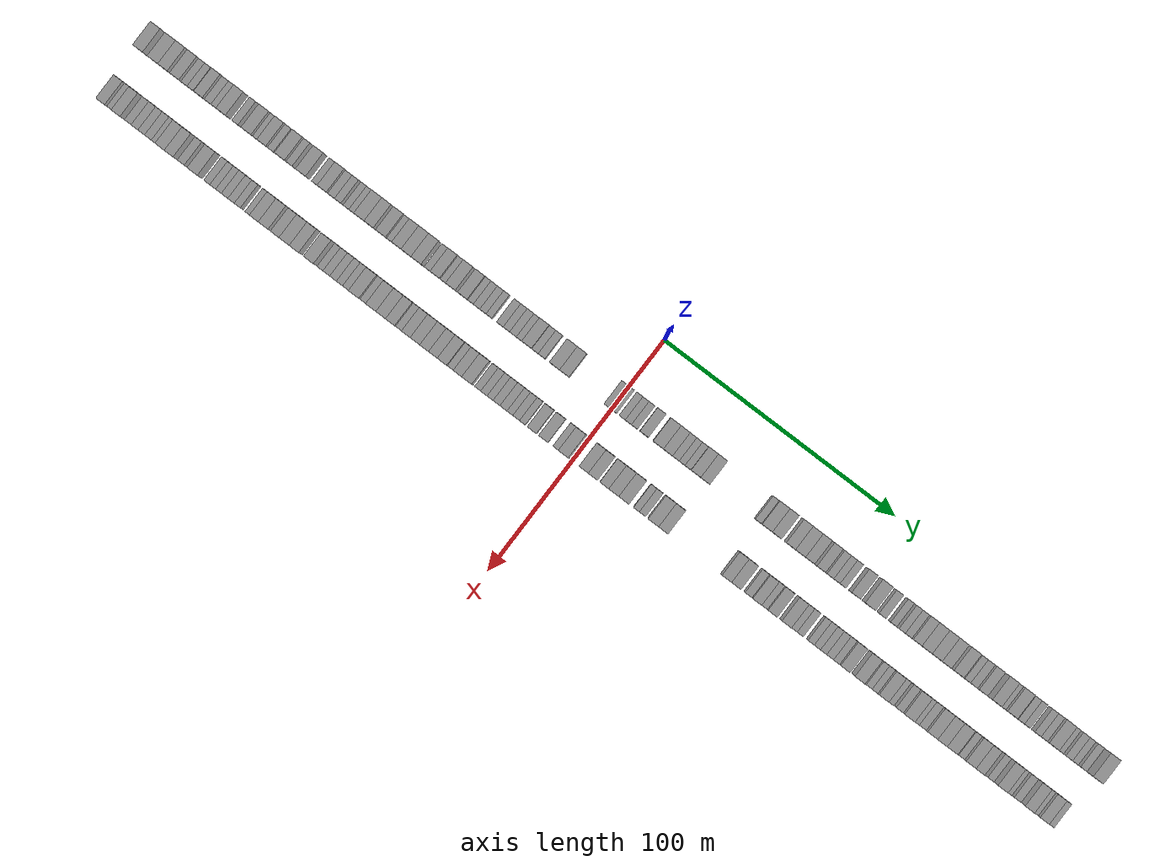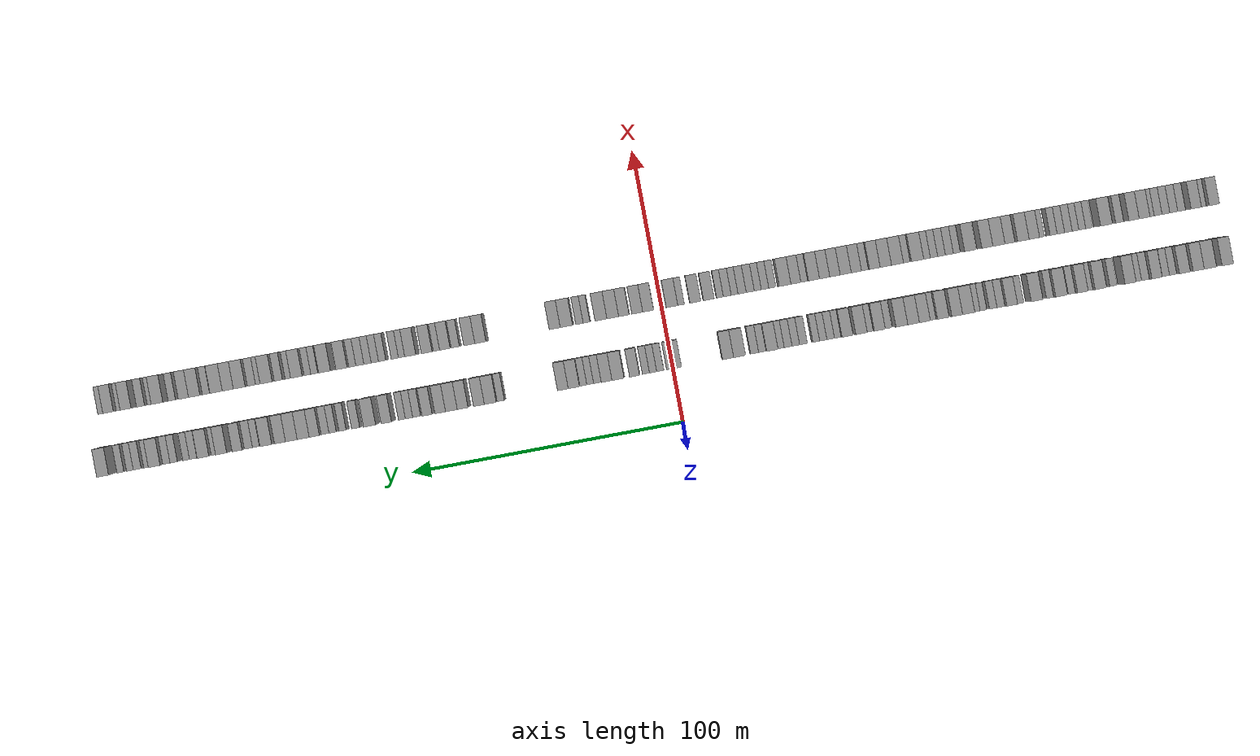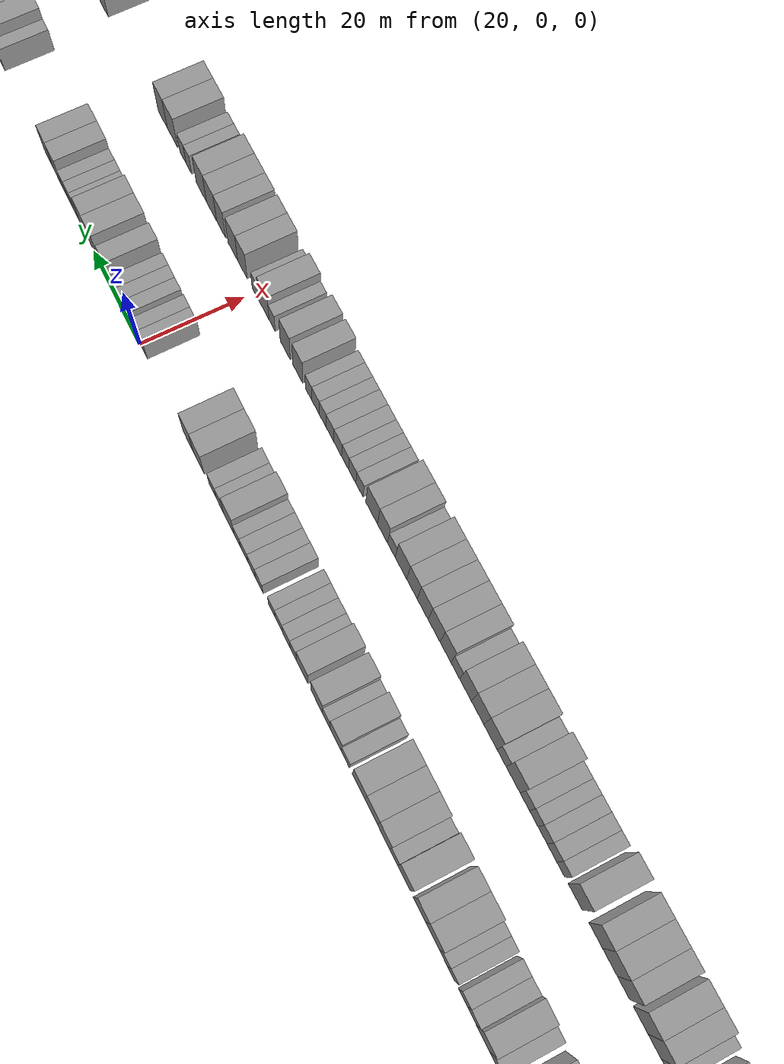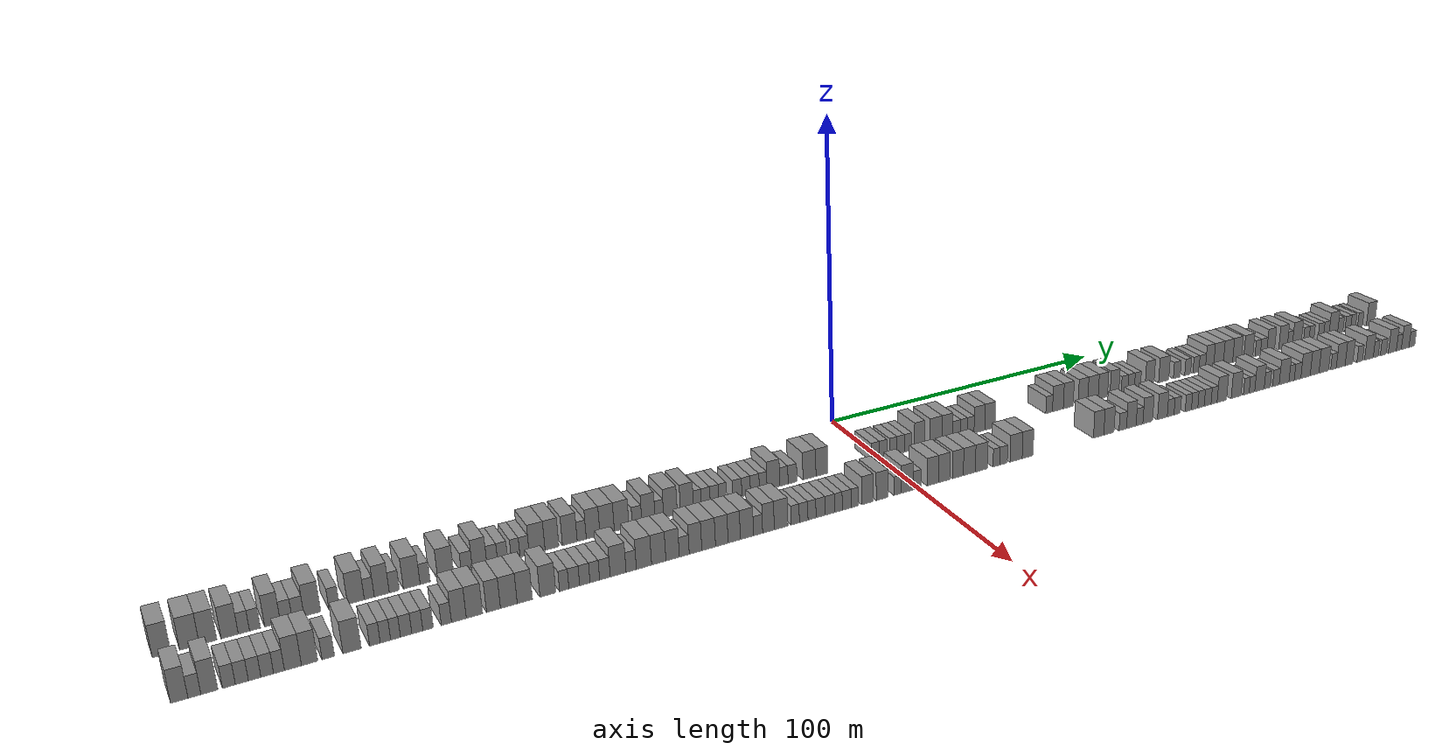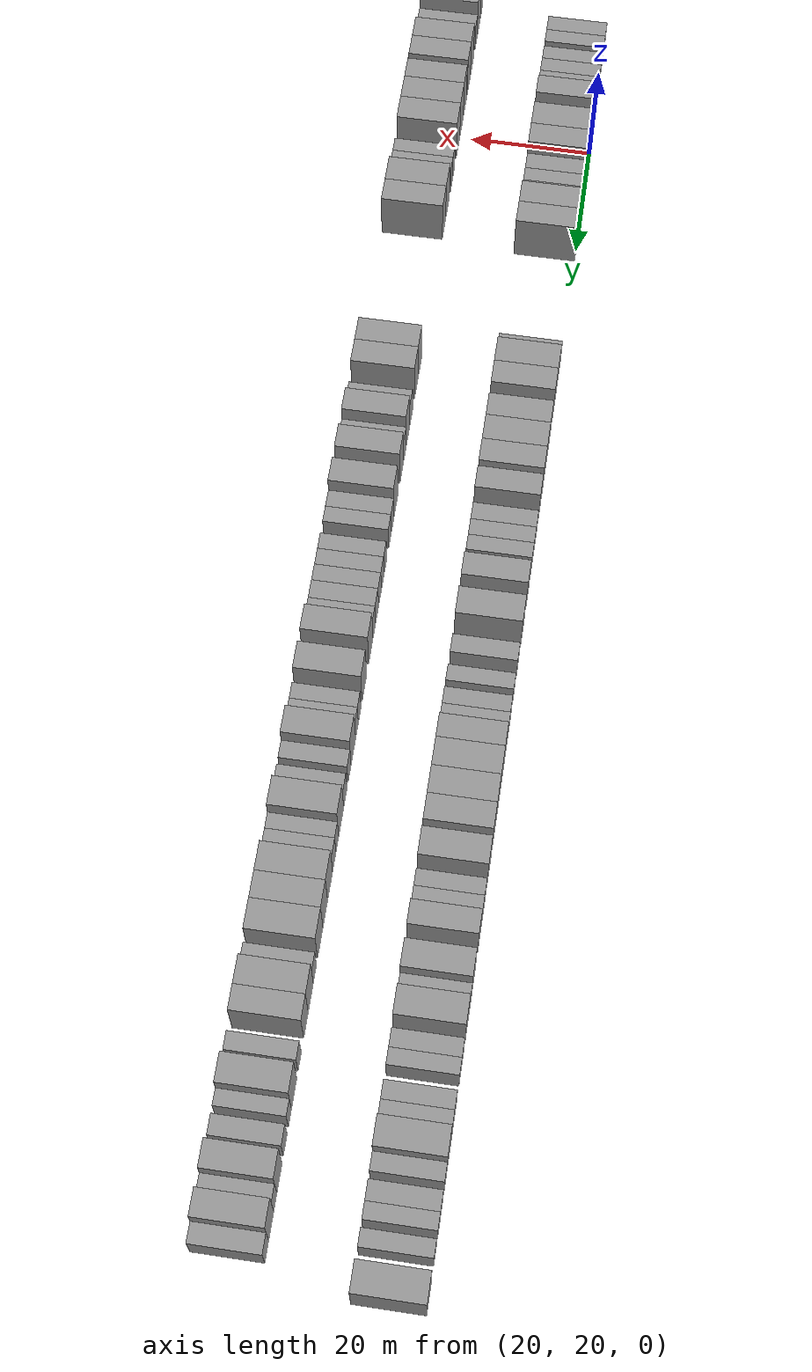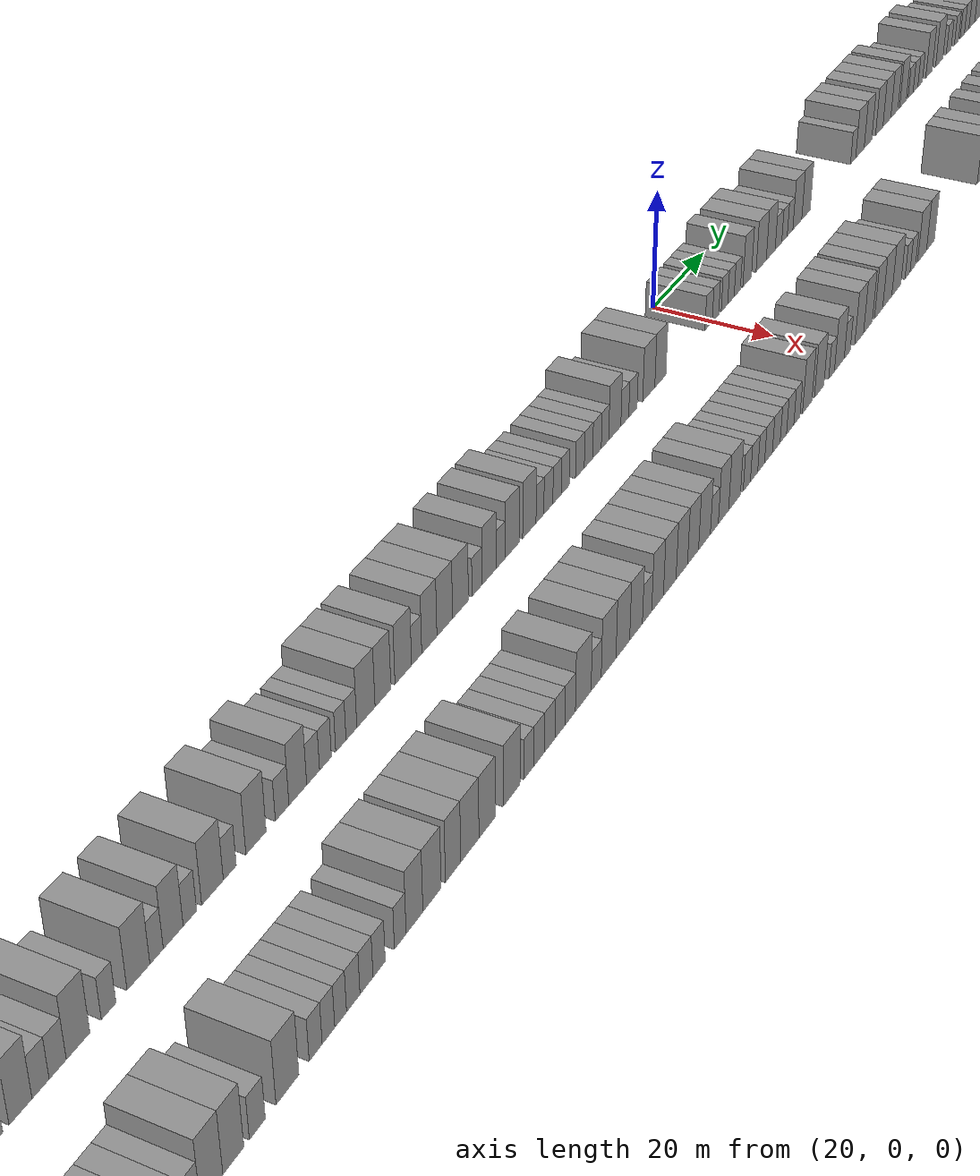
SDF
<sdf version="1.6">
 <world name="default">
  <scene>
   <sky><clouds><speed>12</speed></clouds></sky>
   <ambient>0.4 0.4 0.4 1</ambient>
   <background>0.7 0.7 0.7 1</background>
   <shadows>1</shadows>
  </scene>
  <gravity>0 0 -9.8066</gravity>
  <magnetic_field>6e-06 2.3e-05 -4.2e-05</magnetic_field>
  <physics default="0" name="default_physics" type="ode">
   <ode>
    <solver>
     <type>quick</type>
     <iters>10</iters>
     <sor>1.0</sor>
     <use_dynamic_moi_rescaling>0</use_dynamic_moi_rescaling>
    </solver>
    <constraints>
     <cfm>0</cfm>
     <erp>0.2</erp>
     <contact_max_correcting_vel>100</contact_max_correcting_vel>
     <contact_surface_layer>0.001</contact_surface_layer>
    </constraints>
   </ode>
   <max_step_size>0.004</max_step_size>
   <real_time_factor>1</real_time_factor>
   <real_time_update_rate>250</real_time_update_rate>
  </physics>
  <light name="sun" type="directional">
   <pose>0 0 10 0 0 0</pose>
   <diffuse>0.8 0.8 0.8 1</diffuse>
   <specular>0.2 0.2 0.2 1</specular>
   <attenuation>
    <range>1000</range>
    <constant>0.9</constant>
    <linear>0.01</linear>
    <quadratic>0.001</quadratic>
   </attenuation>
   <direction>-0.5 0.1 -0.9</direction>
  </light>
  <model name="building_1">
   <static>1</static>
   <pose>25.0000 -201.9067 0 0.000000 0.000000 0.000000</pose>
   <link name="link">
    <pose>0 0 4.50 0 0 0</pose>
    <collision name="collision"><geometry><box><size>10.0000 4.1866 9.0000</size></box></geometry></collision>
    <visual name="visual">
     <cast_shadows>0</cast_shadows>
     <geometry><box><size>10.0000 4.1866 9.0000</size></box></geometry>
     <material>
      <script>
       <uri>model://grey_wall/materials/scripts</uri>
       <uri>model://grey_wall/materials/textures</uri>
       <name>vrc/grey_wall</name>
      </script>
     </material>
    </visual>
   </link>
  </model>
  <model name="building_2">
   <static>1</static>
   <pose>25.0000 -195.5699 0 0.000000 0.000000 0.000000</pose>
   <link name="link">
    <pose>0 0 4.50 0 0 0</pose>
    <collision name="collision"><geometry><box><size>10.0000 4.4871 9.0000</size></box></geometry></collision>
    <visual name="visual">
     <cast_shadows>0</cast_shadows>
     <geometry><box><size>10.0000 4.4871 9.0000</size></box></geometry>
     <material>
      <script>
       <uri>model://grey_wall/materials/scripts</uri>
       <uri>model://grey_wall/materials/textures</uri>
       <name>vrc/grey_wall</name>
      </script>
     </material>
    </visual>
   </link>
  </model>
  <model name="building_3">
   <static>1</static>
   <pose>25.0000 -191.3050 0 0.000000 0.000000 0.000000</pose>
   <link name="link">
    <pose>0 0 4.50 0 0 0</pose>
    <collision name="collision"><geometry><box><size>10.0000 4.0426 9.0000</size></box></geometry></collision>
    <visual name="visual">
     <cast_shadows>0</cast_shadows>
     <geometry><box><size>10.0000 4.0426 9.0000</size></box></geometry>
     <material>
      <script>
       <uri>model://grey_wall/materials/scripts</uri>
       <uri>model://grey_wall/materials/textures</uri>
       <name>vrc/grey_wall</name>
      </script>
     </material>
    </visual>
   </link>
  </model>
  <model name="building_4">
   <static>1</static>
   <pose>25.0000 -186.2852 0 0.000000 0.000000 0.000000</pose>
   <link name="link">
    <pose>0 0 4.50 0 0 0</pose>
    <collision name="collision"><geometry><box><size>10.0000 3.9970 9.0000</size></box></geometry></collision>
    <visual name="visual">
     <cast_shadows>0</cast_shadows>
     <geometry><box><size>10.0000 3.9970 9.0000</size></box></geometry>
     <material>
      <script>
       <uri>model://grey_wall/materials/scripts</uri>
       <uri>model://grey_wall/materials/textures</uri>
       <name>vrc/grey_wall</name>
      </script>
     </material>
    </visual>
   </link>
  </model>
  <model name="building_5">
   <static>1</static>
   <pose>25.0000 -182.9670 0 0.000000 0.000000 0.000000</pose>
   <link name="link">
    <pose>0 0 3.00 0 0 0</pose>
    <collision name="collision"><geometry><box><size>10.0000 2.6395 6.0000</size></box></geometry></collision>
    <visual name="visual">
     <cast_shadows>0</cast_shadows>
     <geometry><box><size>10.0000 2.6395 6.0000</size></box></geometry>
     <material>
      <script>
       <uri>model://grey_wall/materials/scripts</uri>
       <uri>model://grey_wall/materials/textures</uri>
       <name>vrc/grey_wall</name>
      </script>
     </material>
    </visual>
   </link>
  </model>
  <model name="building_6">
   <static>1</static>
   <pose>25.0000 -180.3397 0 0.000000 0.000000 0.000000</pose>
   <link name="link">
    <pose>0 0 3.00 0 0 0</pose>
    <collision name="collision"><geometry><box><size>10.0000 2.6151 6.0000</size></box></geometry></collision>
    <visual name="visual">
     <cast_shadows>0</cast_shadows>
     <geometry><box><size>10.0000 2.6151 6.0000</size></box></geometry>
     <material>
      <script>
       <uri>model://grey_wall/materials/scripts</uri>
       <uri>model://grey_wall/materials/textures</uri>
       <name>vrc/grey_wall</name>
      </script>
     </material>
    </visual>
   </link>
  </model>
  <model name="building_7">
   <static>1</static>
   <pose>25.0000 -176.1576 0 0.000000 0.000000 0.000000</pose>
   <link name="link">
    <pose>0 0 4.50 0 0 0</pose>
    <collision name="collision"><geometry><box><size>10.0000 3.7491 9.0000</size></box></geometry></collision>
    <visual name="visual">
     <cast_shadows>0</cast_shadows>
     <geometry><box><size>10.0000 3.7491 9.0000</size></box></geometry>
     <material>
      <script>
       <uri>model://grey_wall/materials/scripts</uri>
       <uri>model://grey_wall/materials/textures</uri>
       <name>vrc/grey_wall</name>
      </script>
     </material>
    </visual>
   </link>
  </model>
  <model name="building_8">
   <static>1</static>
   <pose>25.0000 -172.8619 0 0.000000 0.000000 0.000000</pose>
   <link name="link">
    <pose>0 0 3.00 0 0 0</pose>
    <collision name="collision"><geometry><box><size>10.0000 2.8423 6.0000</size></box></geometry></collision>
    <visual name="visual">
     <cast_shadows>0</cast_shadows>
     <geometry><box><size>10.0000 2.8423 6.0000</size></box></geometry>
     <material>
      <script>
       <uri>model://grey_wall/materials/scripts</uri>
       <uri>model://grey_wall/materials/textures</uri>
       <name>vrc/grey_wall</name>
      </script>
     </material>
    </visual>
   </link>
  </model>
  <model name="building_9">
   <static>1</static>
   <pose>25.0000 -169.9930 0 0.000000 0.000000 0.000000</pose>
   <link name="link">
    <pose>0 0 3.00 0 0 0</pose>
    <collision name="collision"><geometry><box><size>10.0000 2.8954 6.0000</size></box></geometry></collision>
    <visual name="visual">
     <cast_shadows>0</cast_shadows>
     <geometry><box><size>10.0000 2.8954 6.0000</size></box></geometry>
     <material>
      <script>
       <uri>model://grey_wall/materials/scripts</uri>
       <uri>model://grey_wall/materials/textures</uri>
       <name>vrc/grey_wall</name>
      </script>
     </material>
    </visual>
   </link>
  </model>
  <model name="building_10">
   <static>1</static>
   <pose>25.0000 -166.5042 0 0.000000 0.000000 0.000000</pose>
   <link name="link">
    <pose>0 0 4.50 0 0 0</pose>
    <collision name="collision"><geometry><box><size>10.0000 4.0820 9.0000</size></box></geometry></collision>
    <visual name="visual">
     <cast_shadows>0</cast_shadows>
     <geometry><box><size>10.0000 4.0820 9.0000</size></box></geometry>
     <material>
      <script>
       <uri>model://grey_wall/materials/scripts</uri>
       <uri>model://grey_wall/materials/textures</uri>
       <name>vrc/grey_wall</name>
      </script>
     </material>
    </visual>
   </link>
  </model>
  <model name="building_11">
   <static>1</static>
   <pose>25.0000 -161.1423 0 0.000000 0.000000 0.000000</pose>
   <link name="link">
    <pose>0 0 3.00 0 0 0</pose>
    <collision name="collision"><geometry><box><size>10.0000 2.6419 6.0000</size></box></geometry></collision>
    <visual name="visual">
     <cast_shadows>0</cast_shadows>
     <geometry><box><size>10.0000 2.6419 6.0000</size></box></geometry>
     <material>
      <script>
       <uri>model://grey_wall/materials/scripts</uri>
       <uri>model://grey_wall/materials/textures</uri>
       <name>vrc/grey_wall</name>
      </script>
     </material>
    </visual>
   </link>
  </model>
  <model name="building_12">
   <static>1</static>
   <pose>25.0000 -155.7077 0 0.000000 0.000000 0.000000</pose>
   <link name="link">
    <pose>0 0 4.50 0 0 0</pose>
    <collision name="collision"><geometry><box><size>10.0000 4.2272 9.0000</size></box></geometry></collision>
    <visual name="visual">
     <cast_shadows>0</cast_shadows>
     <geometry><box><size>10.0000 4.2272 9.0000</size></box></geometry>
     <material>
      <script>
       <uri>model://grey_wall/materials/scripts</uri>
       <uri>model://grey_wall/materials/textures</uri>
       <name>vrc/grey_wall</name>
      </script>
     </material>
    </visual>
   </link>
  </model>
  <model name="building_13">
   <static>1</static>
   <pose>25.0000 -152.3350 0 0.000000 0.000000 0.000000</pose>
   <link name="link">
    <pose>0 0 3.00 0 0 0</pose>
    <collision name="collision"><geometry><box><size>10.0000 2.5183 6.0000</size></box></geometry></collision>
    <visual name="visual">
     <cast_shadows>0</cast_shadows>
     <geometry><box><size>10.0000 2.5183 6.0000</size></box></geometry>
     <material>
      <script>
       <uri>model://grey_wall/materials/scripts</uri>
       <uri>model://grey_wall/materials/textures</uri>
       <name>vrc/grey_wall</name>
      </script>
     </material>
    </visual>
   </link>
  </model>
  <model name="building_14">
   <static>1</static>
   <pose>25.0000 -149.1588 0 0.000000 0.000000 0.000000</pose>
   <link name="link">
    <pose>0 0 4.50 0 0 0</pose>
    <collision name="collision"><geometry><box><size>10.0000 3.8340 9.0000</size></box></geometry></collision>
    <visual name="visual">
     <cast_shadows>0</cast_shadows>
     <geometry><box><size>10.0000 3.8340 9.0000</size></box></geometry>
     <material>
      <script>
       <uri>model://grey_wall/materials/scripts</uri>
       <uri>model://grey_wall/materials/textures</uri>
       <name>vrc/grey_wall</name>
      </script>
     </material>
    </visual>
   </link>
  </model>
  <model name="building_15">
   <static>1</static>
   <pose>25.0000 -145.9305 0 0.000000 0.000000 0.000000</pose>
   <link name="link">
    <pose>0 0 3.00 0 0 0</pose>
    <collision name="collision"><geometry><box><size>10.0000 2.6226 6.0000</size></box></geometry></collision>
    <visual name="visual">
     <cast_shadows>0</cast_shadows>
     <geometry><box><size>10.0000 2.6226 6.0000</size></box></geometry>
     <material>
      <script>
       <uri>model://grey_wall/materials/scripts</uri>
       <uri>model://grey_wall/materials/textures</uri>
       <name>vrc/grey_wall</name>
      </script>
     </material>
    </visual>
   </link>
  </model>
  <model name="building_16">
   <static>1</static>
   <pose>25.0000 -141.4418 0 0.000000 0.000000 0.000000</pose>
   <link name="link">
    <pose>0 0 4.50 0 0 0</pose>
    <collision name="collision"><geometry><box><size>10.0000 4.3547 9.0000</size></box></geometry></collision>
    <visual name="visual">
     <cast_shadows>0</cast_shadows>
     <geometry><box><size>10.0000 4.3547 9.0000</size></box></geometry>
     <material>
      <script>
       <uri>model://grey_wall/materials/scripts</uri>
       <uri>model://grey_wall/materials/textures</uri>
       <name>vrc/grey_wall</name>
      </script>
     </material>
    </visual>
   </link>
  </model>
  <model name="building_17">
   <static>1</static>
   <pose>25.0000 -137.9438 0 0.000000 0.000000 0.000000</pose>
   <link name="link">
    <pose>0 0 3.00 0 0 0</pose>
    <collision name="collision"><geometry><box><size>10.0000 2.6413 6.0000</size></box></geometry></collision>
    <visual name="visual">
     <cast_shadows>0</cast_shadows>
     <geometry><box><size>10.0000 2.6413 6.0000</size></box></geometry>
     <material>
      <script>
       <uri>model://grey_wall/materials/scripts</uri>
       <uri>model://grey_wall/materials/textures</uri>
       <name>vrc/grey_wall</name>
      </script>
     </material>
    </visual>
   </link>
  </model>
  <model name="building_18">
   <static>1</static>
   <pose>25.0000 -132.4843 0 0.000000 0.000000 0.000000</pose>
   <link name="link">
    <pose>0 0 4.50 0 0 0</pose>
    <collision name="collision"><geometry><box><size>10.0000 4.2777 9.0000</size></box></geometry></collision>
    <visual name="visual">
     <cast_shadows>0</cast_shadows>
     <geometry><box><size>10.0000 4.2777 9.0000</size></box></geometry>
     <material>
      <script>
       <uri>model://grey_wall/materials/scripts</uri>
       <uri>model://grey_wall/materials/textures</uri>
       <name>vrc/grey_wall</name>
      </script>
     </material>
    </visual>
   </link>
  </model>
  <model name="building_19">
   <static>1</static>
   <pose>25.0000 -126.8623 0 0.000000 0.000000 0.000000</pose>
   <link name="link">
    <pose>0 0 3.00 0 0 0</pose>
    <collision name="collision"><geometry><box><size>10.0000 2.9662 6.0000</size></box></geometry></collision>
    <visual name="visual">
     <cast_shadows>0</cast_shadows>
     <geometry><box><size>10.0000 2.9662 6.0000</size></box></geometry>
     <material>
      <script>
       <uri>model://grey_wall/materials/scripts</uri>
       <uri>model://grey_wall/materials/textures</uri>
       <name>vrc/grey_wall</name>
      </script>
     </material>
    </visual>
   </link>
  </model>
  <model name="building_20">
   <static>1</static>
   <pose>25.0000 -123.4100 0 0.000000 0.000000 0.000000</pose>
   <link name="link">
    <pose>0 0 4.50 0 0 0</pose>
    <collision name="collision"><geometry><box><size>10.0000 3.9384 9.0000</size></box></geometry></collision>
    <visual name="visual">
     <cast_shadows>0</cast_shadows>
     <geometry><box><size>10.0000 3.9384 9.0000</size></box></geometry>
     <material>
      <script>
       <uri>model://grey_wall/materials/scripts</uri>
       <uri>model://grey_wall/materials/textures</uri>
       <name>vrc/grey_wall</name>
      </script>
     </material>
    </visual>
   </link>
  </model>
  <model name="building_21">
   <static>1</static>
   <pose>25.0000 -119.9843 0 0.000000 0.000000 0.000000</pose>
   <link name="link">
    <pose>0 0 3.00 0 0 0</pose>
    <collision name="collision"><geometry><box><size>10.0000 2.9129 6.0000</size></box></geometry></collision>
    <visual name="visual">
     <cast_shadows>0</cast_shadows>
     <geometry><box><size>10.0000 2.9129 6.0000</size></box></geometry>
     <material>
      <script>
       <uri>model://grey_wall/materials/scripts</uri>
       <uri>model://grey_wall/materials/textures</uri>
       <name>vrc/grey_wall</name>
      </script>
     </material>
    </visual>
   </link>
  </model>
  <model name="building_22">
   <static>1</static>
   <pose>25.0000 -117.1585 0 0.000000 0.000000 0.000000</pose>
   <link name="link">
    <pose>0 0 3.00 0 0 0</pose>
    <collision name="collision"><geometry><box><size>10.0000 2.7387 6.0000</size></box></geometry></collision>
    <visual name="visual">
     <cast_shadows>0</cast_shadows>
     <geometry><box><size>10.0000 2.7387 6.0000</size></box></geometry>
     <material>
      <script>
       <uri>model://grey_wall/materials/scripts</uri>
       <uri>model://grey_wall/materials/textures</uri>
       <name>vrc/grey_wall</name>
      </script>
     </material>
    </visual>
   </link>
  </model>
  <model name="building_23">
   <static>1</static>
   <pose>25.0000 -113.5812 0 0.000000 0.000000 0.000000</pose>
   <link name="link">
    <pose>0 0 3.00 0 0 0</pose>
    <collision name="collision"><geometry><box><size>10.0000 2.4157 6.0000</size></box></geometry></collision>
    <visual name="visual">
     <cast_shadows>0</cast_shadows>
     <geometry><box><size>10.0000 2.4157 6.0000</size></box></geometry>
     <material>
      <script>
       <uri>model://grey_wall/materials/scripts</uri>
       <uri>model://grey_wall/materials/textures</uri>
       <name>vrc/grey_wall</name>
      </script>
     </material>
    </visual>
   </link>
  </model>
  <model name="building_24">
   <static>1</static>
   <pose>25.0000 -111.0891 0 0.000000 0.000000 0.000000</pose>
   <link name="link">
    <pose>0 0 3.00 0 0 0</pose>
    <collision name="collision"><geometry><box><size>10.0000 2.5686 6.0000</size></box></geometry></collision>
    <visual name="visual">
     <cast_shadows>0</cast_shadows>
     <geometry><box><size>10.0000 2.5686 6.0000</size></box></geometry>
     <material>
      <script>
       <uri>model://grey_wall/materials/scripts</uri>
       <uri>model://grey_wall/materials/textures</uri>
       <name>vrc/grey_wall</name>
      </script>
     </material>
    </visual>
   </link>
  </model>
  <model name="building_25">
   <static>1</static>
   <pose>25.0000 -107.6011 0 0.000000 0.000000 0.000000</pose>
   <link name="link">
    <pose>0 0 4.50 0 0 0</pose>
    <collision name="collision"><geometry><box><size>10.0000 4.4074 9.0000</size></box></geometry></collision>
    <visual name="visual">
     <cast_shadows>0</cast_shadows>
     <geometry><box><size>10.0000 4.4074 9.0000</size></box></geometry>
     <material>
      <script>
       <uri>model://grey_wall/materials/scripts</uri>
       <uri>model://grey_wall/materials/textures</uri>
       <name>vrc/grey_wall</name>
      </script>
     </material>
    </visual>
   </link>
  </model>
  <model name="building_26">
   <static>1</static>
   <pose>25.0000 -103.4328 0 0.000000 0.000000 0.000000</pose>
   <link name="link">
    <pose>0 0 4.50 0 0 0</pose>
    <collision name="collision"><geometry><box><size>10.0000 3.9291 9.0000</size></box></geometry></collision>
    <visual name="visual">
     <cast_shadows>0</cast_shadows>
     <geometry><box><size>10.0000 3.9291 9.0000</size></box></geometry>
     <material>
      <script>
       <uri>model://grey_wall/materials/scripts</uri>
       <uri>model://grey_wall/materials/textures</uri>
       <name>vrc/grey_wall</name>
      </script>
     </material>
    </visual>
   </link>
  </model>
  <model name="building_27">
   <static>1</static>
   <pose>25.0000 -98.3525 0 0.000000 0.000000 0.000000</pose>
   <link name="link">
    <pose>0 0 4.50 0 0 0</pose>
    <collision name="collision"><geometry><box><size>10.0000 4.2314 9.0000</size></box></geometry></collision>
    <visual name="visual">
     <cast_shadows>0</cast_shadows>
     <geometry><box><size>10.0000 4.2314 9.0000</size></box></geometry>
     <material>
      <script>
       <uri>model://grey_wall/materials/scripts</uri>
       <uri>model://grey_wall/materials/textures</uri>
       <name>vrc/grey_wall</name>
      </script>
     </material>
    </visual>
   </link>
  </model>
  <model name="building_28">
   <static>1</static>
   <pose>25.0000 -94.9310 0 0.000000 0.000000 0.000000</pose>
   <link name="link">
    <pose>0 0 3.00 0 0 0</pose>
    <collision name="collision"><geometry><box><size>10.0000 2.6116 6.0000</size></box></geometry></collision>
    <visual name="visual">
     <cast_shadows>0</cast_shadows>
     <geometry><box><size>10.0000 2.6116 6.0000</size></box></geometry>
     <material>
      <script>
       <uri>model://grey_wall/materials/scripts</uri>
       <uri>model://grey_wall/materials/textures</uri>
       <name>vrc/grey_wall</name>
      </script>
     </material>
    </visual>
   </link>
  </model>
  <model name="building_29">
   <static>1</static>
   <pose>25.0000 -91.6338 0 0.000000 0.000000 0.000000</pose>
   <link name="link">
    <pose>0 0 4.50 0 0 0</pose>
    <collision name="collision"><geometry><box><size>10.0000 3.9828 9.0000</size></box></geometry></collision>
    <visual name="visual">
     <cast_shadows>0</cast_shadows>
     <geometry><box><size>10.0000 3.9828 9.0000</size></box></geometry>
     <material>
      <script>
       <uri>model://grey_wall/materials/scripts</uri>
       <uri>model://grey_wall/materials/textures</uri>
       <name>vrc/grey_wall</name>
      </script>
     </material>
    </visual>
   </link>
  </model>
  <model name="building_30">
   <static>1</static>
   <pose>25.0000 -87.5377 0 0.000000 0.000000 0.000000</pose>
   <link name="link">
    <pose>0 0 4.50 0 0 0</pose>
    <collision name="collision"><geometry><box><size>10.0000 4.2092 9.0000</size></box></geometry></collision>
    <visual name="visual">
     <cast_shadows>0</cast_shadows>
     <geometry><box><size>10.0000 4.2092 9.0000</size></box></geometry>
     <material>
      <script>
       <uri>model://grey_wall/materials/scripts</uri>
       <uri>model://grey_wall/materials/textures</uri>
       <name>vrc/grey_wall</name>
      </script>
     </material>
    </visual>
   </link>
  </model>
  <model name="building_31">
   <static>1</static>
   <pose>25.0000 -83.2692 0 0.000000 0.000000 0.000000</pose>
   <link name="link">
    <pose>0 0 4.50 0 0 0</pose>
    <collision name="collision"><geometry><box><size>10.0000 4.3280 9.0000</size></box></geometry></collision>
    <visual name="visual">
     <cast_shadows>0</cast_shadows>
     <geometry><box><size>10.0000 4.3280 9.0000</size></box></geometry>
     <material>
      <script>
       <uri>model://grey_wall/materials/scripts</uri>
       <uri>model://grey_wall/materials/textures</uri>
       <name>vrc/grey_wall</name>
      </script>
     </material>
    </visual>
   </link>
  </model>
  <model name="building_32">
   <static>1</static>
   <pose>25.0000 -78.6781 0 0.000000 0.000000 0.000000</pose>
   <link name="link">
    <pose>0 0 3.00 0 0 0</pose>
    <collision name="collision"><geometry><box><size>10.0000 2.8541 6.0000</size></box></geometry></collision>
    <visual name="visual">
     <cast_shadows>0</cast_shadows>
     <geometry><box><size>10.0000 2.8541 6.0000</size></box></geometry>
     <material>
      <script>
       <uri>model://grey_wall/materials/scripts</uri>
       <uri>model://grey_wall/materials/textures</uri>
       <name>vrc/grey_wall</name>
      </script>
     </material>
    </visual>
   </link>
  </model>
  <model name="building_33">
   <static>1</static>
   <pose>25.0000 -75.2485 0 0.000000 0.000000 0.000000</pose>
   <link name="link">
    <pose>0 0 4.50 0 0 0</pose>
    <collision name="collision"><geometry><box><size>10.0000 4.0050 9.0000</size></box></geometry></collision>
    <visual name="visual">
     <cast_shadows>0</cast_shadows>
     <geometry><box><size>10.0000 4.0050 9.0000</size></box></geometry>
     <material>
      <script>
       <uri>model://grey_wall/materials/scripts</uri>
       <uri>model://grey_wall/materials/textures</uri>
       <name>vrc/grey_wall</name>
      </script>
     </material>
    </visual>
   </link>
  </model>
  <model name="building_34">
   <static>1</static>
   <pose>25.0000 -71.9568 0 0.000000 0.000000 0.000000</pose>
   <link name="link">
    <pose>0 0 3.00 0 0 0</pose>
    <collision name="collision"><geometry><box><size>10.0000 2.5785 6.0000</size></box></geometry></collision>
    <visual name="visual">
     <cast_shadows>0</cast_shadows>
     <geometry><box><size>10.0000 2.5785 6.0000</size></box></geometry>
     <material>
      <script>
       <uri>model://grey_wall/materials/scripts</uri>
       <uri>model://grey_wall/materials/textures</uri>
       <name>vrc/grey_wall</name>
      </script>
     </material>
    </visual>
   </link>
  </model>
  <model name="building_35">
   <static>1</static>
   <pose>25.0000 -68.5935 0 0.000000 0.000000 0.000000</pose>
   <link name="link">
    <pose>0 0 4.50 0 0 0</pose>
    <collision name="collision"><geometry><box><size>10.0000 4.1481 9.0000</size></box></geometry></collision>
    <visual name="visual">
     <cast_shadows>0</cast_shadows>
     <geometry><box><size>10.0000 4.1481 9.0000</size></box></geometry>
     <material>
      <script>
       <uri>model://grey_wall/materials/scripts</uri>
       <uri>model://grey_wall/materials/textures</uri>
       <name>vrc/grey_wall</name>
      </script>
     </material>
    </visual>
   </link>
  </model>
  <model name="building_36">
   <static>1</static>
   <pose>25.0000 -63.5018 0 0.000000 0.000000 0.000000</pose>
   <link name="link">
    <pose>0 0 4.50 0 0 0</pose>
    <collision name="collision"><geometry><box><size>10.0000 4.0353 9.0000</size></box></geometry></collision>
    <visual name="visual">
     <cast_shadows>0</cast_shadows>
     <geometry><box><size>10.0000 4.0353 9.0000</size></box></geometry>
     <material>
      <script>
       <uri>model://grey_wall/materials/scripts</uri>
       <uri>model://grey_wall/materials/textures</uri>
       <name>vrc/grey_wall</name>
      </script>
     </material>
    </visual>
   </link>
  </model>
  <model name="building_37">
   <static>1</static>
   <pose>25.0000 -60.2751 0 0.000000 0.000000 0.000000</pose>
   <link name="link">
    <pose>0 0 3.00 0 0 0</pose>
    <collision name="collision"><geometry><box><size>10.0000 2.4179 6.0000</size></box></geometry></collision>
    <visual name="visual">
     <cast_shadows>0</cast_shadows>
     <geometry><box><size>10.0000 2.4179 6.0000</size></box></geometry>
     <material>
      <script>
       <uri>model://grey_wall/materials/scripts</uri>
       <uri>model://grey_wall/materials/textures</uri>
       <name>vrc/grey_wall</name>
      </script>
     </material>
    </visual>
   </link>
  </model>
  <model name="building_38">
   <static>1</static>
   <pose>25.0000 -57.6780 0 0.000000 0.000000 0.000000</pose>
   <link name="link">
    <pose>0 0 3.00 0 0 0</pose>
    <collision name="collision"><geometry><box><size>10.0000 2.7763 6.0000</size></box></geometry></collision>
    <visual name="visual">
     <cast_shadows>0</cast_shadows>
     <geometry><box><size>10.0000 2.7763 6.0000</size></box></geometry>
     <material>
      <script>
       <uri>model://grey_wall/materials/scripts</uri>
       <uri>model://grey_wall/materials/textures</uri>
       <name>vrc/grey_wall</name>
      </script>
     </material>
    </visual>
   </link>
  </model>
  <model name="building_39">
   <static>1</static>
   <pose>25.0000 -54.9650 0 0.000000 0.000000 0.000000</pose>
   <link name="link">
    <pose>0 0 3.00 0 0 0</pose>
    <collision name="collision"><geometry><box><size>10.0000 2.6498 6.0000</size></box></geometry></collision>
    <visual name="visual">
     <cast_shadows>0</cast_shadows>
     <geometry><box><size>10.0000 2.6498 6.0000</size></box></geometry>
     <material>
      <script>
       <uri>model://grey_wall/materials/scripts</uri>
       <uri>model://grey_wall/materials/textures</uri>
       <name>vrc/grey_wall</name>
      </script>
     </material>
    </visual>
   </link>
  </model>
  <model name="building_40">
   <static>1</static>
   <pose>25.0000 -52.3989 0 0.000000 0.000000 0.000000</pose>
   <link name="link">
    <pose>0 0 3.00 0 0 0</pose>
    <collision name="collision"><geometry><box><size>10.0000 2.4823 6.0000</size></box></geometry></collision>
    <visual name="visual">
     <cast_shadows>0</cast_shadows>
     <geometry><box><size>10.0000 2.4823 6.0000</size></box></geometry>
     <material>
      <script>
       <uri>model://grey_wall/materials/scripts</uri>
       <uri>model://grey_wall/materials/textures</uri>
       <name>vrc/grey_wall</name>
      </script>
     </material>
    </visual>
   </link>
  </model>
  <model name="building_41">
   <static>1</static>
   <pose>25.0000 -47.7255 0 0.000000 0.000000 0.000000</pose>
   <link name="link">
    <pose>0 0 3.00 0 0 0</pose>
    <collision name="collision"><geometry><box><size>10.0000 2.8646 6.0000</size></box></geometry></collision>
    <visual name="visual">
     <cast_shadows>0</cast_shadows>
     <geometry><box><size>10.0000 2.8646 6.0000</size></box></geometry>
     <material>
      <script>
       <uri>model://grey_wall/materials/scripts</uri>
       <uri>model://grey_wall/materials/textures</uri>
       <name>vrc/grey_wall</name>
      </script>
     </material>
    </visual>
   </link>
  </model>
  <model name="building_42">
   <static>1</static>
   <pose>25.0000 -44.9160 0 0.000000 0.000000 0.000000</pose>
   <link name="link">
    <pose>0 0 3.00 0 0 0</pose>
    <collision name="collision"><geometry><box><size>10.0000 2.7545 6.0000</size></box></geometry></collision>
    <visual name="visual">
     <cast_shadows>0</cast_shadows>
     <geometry><box><size>10.0000 2.7545 6.0000</size></box></geometry>
     <material>
      <script>
       <uri>model://grey_wall/materials/scripts</uri>
       <uri>model://grey_wall/materials/textures</uri>
       <name>vrc/grey_wall</name>
      </script>
     </material>
    </visual>
   </link>
  </model>
  <model name="building_43">
   <static>1</static>
   <pose>25.0000 -42.1074 0 0.000000 0.000000 0.000000</pose>
   <link name="link">
    <pose>0 0 3.00 0 0 0</pose>
    <collision name="collision"><geometry><box><size>10.0000 2.8627 6.0000</size></box></geometry></collision>
    <visual name="visual">
     <cast_shadows>0</cast_shadows>
     <geometry><box><size>10.0000 2.8627 6.0000</size></box></geometry>
     <material>
      <script>
       <uri>model://grey_wall/materials/scripts</uri>
       <uri>model://grey_wall/materials/textures</uri>
       <name>vrc/grey_wall</name>
      </script>
     </material>
    </visual>
   </link>
  </model>
  <model name="building_44">
   <static>1</static>
   <pose>25.0000 -39.4334 0 0.000000 0.000000 0.000000</pose>
   <link name="link">
    <pose>0 0 3.00 0 0 0</pose>
    <collision name="collision"><geometry><box><size>10.0000 2.4853 6.0000</size></box></geometry></collision>
    <visual name="visual">
     <cast_shadows>0</cast_shadows>
     <geometry><box><size>10.0000 2.4853 6.0000</size></box></geometry>
     <material>
      <script>
       <uri>model://grey_wall/materials/scripts</uri>
       <uri>model://grey_wall/materials/textures</uri>
       <name>vrc/grey_wall</name>
      </script>
     </material>
    </visual>
   </link>
  </model>
  <model name="building_45">
   <static>1</static>
   <pose>25.0000 -36.1149 0 0.000000 0.000000 0.000000</pose>
   <link name="link">
    <pose>0 0 4.50 0 0 0</pose>
    <collision name="collision"><geometry><box><size>10.0000 4.1516 9.0000</size></box></geometry></collision>
    <visual name="visual">
     <cast_shadows>0</cast_shadows>
     <geometry><box><size>10.0000 4.1516 9.0000</size></box></geometry>
     <material>
      <script>
       <uri>model://grey_wall/materials/scripts</uri>
       <uri>model://grey_wall/materials/textures</uri>
       <name>vrc/grey_wall</name>
      </script>
     </material>
    </visual>
   </link>
  </model>
  <model name="building_46">
   <static>1</static>
   <pose>25.0000 -32.6743 0 0.000000 0.000000 0.000000</pose>
   <link name="link">
    <pose>0 0 3.00 0 0 0</pose>
    <collision name="collision"><geometry><box><size>10.0000 2.7298 6.0000</size></box></geometry></collision>
    <visual name="visual">
     <cast_shadows>0</cast_shadows>
     <geometry><box><size>10.0000 2.7298 6.0000</size></box></geometry>
     <material>
      <script>
       <uri>model://grey_wall/materials/scripts</uri>
       <uri>model://grey_wall/materials/textures</uri>
       <name>vrc/grey_wall</name>
      </script>
     </material>
    </visual>
   </link>
  </model>
  <model name="building_47">
   <static>1</static>
   <pose>25.0000 -29.8461 0 0.000000 0.000000 0.000000</pose>
   <link name="link">
    <pose>0 0 3.00 0 0 0</pose>
    <collision name="collision"><geometry><box><size>10.0000 2.9266 6.0000</size></box></geometry></collision>
    <visual name="visual">
     <cast_shadows>0</cast_shadows>
     <geometry><box><size>10.0000 2.9266 6.0000</size></box></geometry>
     <material>
      <script>
       <uri>model://grey_wall/materials/scripts</uri>
       <uri>model://grey_wall/materials/textures</uri>
       <name>vrc/grey_wall</name>
      </script>
     </material>
    </visual>
   </link>
  </model>
  <model name="building_48">
   <static>1</static>
   <pose>25.0000 -24.2076 0 0.000000 0.000000 0.000000</pose>
   <link name="link">
    <pose>0 0 4.50 0 0 0</pose>
    <collision name="collision"><geometry><box><size>10.0000 4.3504 9.0000</size></box></geometry></collision>
    <visual name="visual">
     <cast_shadows>0</cast_shadows>
     <geometry><box><size>10.0000 4.3504 9.0000</size></box></geometry>
     <material>
      <script>
       <uri>model://grey_wall/materials/scripts</uri>
       <uri>model://grey_wall/materials/textures</uri>
       <name>vrc/grey_wall</name>
      </script>
     </material>
    </visual>
   </link>
  </model>
  <model name="building_49">
   <static>1</static>
   <pose>25.0000 -20.0120 0 0.000000 0.000000 0.000000</pose>
   <link name="link">
    <pose>0 0 4.50 0 0 0</pose>
    <collision name="collision"><geometry><box><size>10.0000 4.0408 9.0000</size></box></geometry></collision>
    <visual name="visual">
     <cast_shadows>0</cast_shadows>
     <geometry><box><size>10.0000 4.0408 9.0000</size></box></geometry>
     <material>
      <script>
       <uri>model://grey_wall/materials/scripts</uri>
       <uri>model://grey_wall/materials/textures</uri>
       <name>vrc/grey_wall</name>
      </script>
     </material>
    </visual>
   </link>
  </model>
  <model name="building_50">
   <static>1</static>
   <pose>25.0000 -1.6596 0 0.000000 0.000000 0.000000</pose>
   <link name="link">
    <pose>0 0 3.00 0 0 0</pose>
    <collision name="collision"><geometry><box><size>10.0000 2.8880 6.0000</size></box></geometry></collision>
    <visual name="visual">
     <cast_shadows>0</cast_shadows>
     <geometry><box><size>10.0000 2.8880 6.0000</size></box></geometry>
     <material>
      <script>
       <uri>model://grey_wall/materials/scripts</uri>
       <uri>model://grey_wall/materials/textures</uri>
       <name>vrc/grey_wall</name>
      </script>
     </material>
    </visual>
   </link>
  </model>
  <model name="building_51">
   <static>1</static>
   <pose>25.0000 1.0819 0 0.000000 0.000000 0.000000</pose>
   <link name="link">
    <pose>0 0 3.00 0 0 0</pose>
    <collision name="collision"><geometry><box><size>10.0000 2.5949 6.0000</size></box></geometry></collision>
    <visual name="visual">
     <cast_shadows>0</cast_shadows>
     <geometry><box><size>10.0000 2.5949 6.0000</size></box></geometry>
     <material>
      <script>
       <uri>model://grey_wall/materials/scripts</uri>
       <uri>model://grey_wall/materials/textures</uri>
       <name>vrc/grey_wall</name>
      </script>
     </material>
    </visual>
   </link>
  </model>
  <model name="building_52">
   <static>1</static>
   <pose>25.0000 4.6822 0 0.000000 0.000000 0.000000</pose>
   <link name="link">
    <pose>0 0 3.00 0 0 0</pose>
    <collision name="collision"><geometry><box><size>10.0000 2.6058 6.0000</size></box></geometry></collision>
    <visual name="visual">
     <cast_shadows>0</cast_shadows>
     <geometry><box><size>10.0000 2.6058 6.0000</size></box></geometry>
     <material>
      <script>
       <uri>model://grey_wall/materials/scripts</uri>
       <uri>model://grey_wall/materials/textures</uri>
       <name>vrc/grey_wall</name>
      </script>
     </material>
    </visual>
   </link>
  </model>
  <model name="building_53">
   <static>1</static>
   <pose>25.0000 7.3103 0 0.000000 0.000000 0.000000</pose>
   <link name="link">
    <pose>0 0 3.00 0 0 0</pose>
    <collision name="collision"><geometry><box><size>10.0000 2.6505 6.0000</size></box></geometry></collision>
    <visual name="visual">
     <cast_shadows>0</cast_shadows>
     <geometry><box><size>10.0000 2.6505 6.0000</size></box></geometry>
     <material>
      <script>
       <uri>model://grey_wall/materials/scripts</uri>
       <uri>model://grey_wall/materials/textures</uri>
       <name>vrc/grey_wall</name>
      </script>
     </material>
    </visual>
   </link>
  </model>
  <model name="building_54">
   <static>1</static>
   <pose>25.0000 9.9324 0 0.000000 0.000000 0.000000</pose>
   <link name="link">
    <pose>0 0 3.00 0 0 0</pose>
    <collision name="collision"><geometry><box><size>10.0000 2.5936 6.0000</size></box></geometry></collision>
    <visual name="visual">
     <cast_shadows>0</cast_shadows>
     <geometry><box><size>10.0000 2.5936 6.0000</size></box></geometry>
     <material>
      <script>
       <uri>model://grey_wall/materials/scripts</uri>
       <uri>model://grey_wall/materials/textures</uri>
       <name>vrc/grey_wall</name>
      </script>
     </material>
    </visual>
   </link>
  </model>
  <model name="building_55">
   <static>1</static>
   <pose>25.0000 14.0407 0 0.000000 0.000000 0.000000</pose>
   <link name="link">
    <pose>0 0 4.50 0 0 0</pose>
    <collision name="collision"><geometry><box><size>10.0000 3.6229 9.0000</size></box></geometry></collision>
    <visual name="visual">
     <cast_shadows>0</cast_shadows>
     <geometry><box><size>10.0000 3.6229 9.0000</size></box></geometry>
     <material>
      <script>
       <uri>model://grey_wall/materials/scripts</uri>
       <uri>model://grey_wall/materials/textures</uri>
       <name>vrc/grey_wall</name>
      </script>
     </material>
    </visual>
   </link>
  </model>
  <model name="building_56">
   <static>1</static>
   <pose>25.0000 20.0554 0 0.000000 0.000000 0.000000</pose>
   <link name="link">
    <pose>0 0 4.50 0 0 0</pose>
    <collision name="collision"><geometry><box><size>10.0000 4.4065 9.0000</size></box></geometry></collision>
    <visual name="visual">
     <cast_shadows>0</cast_shadows>
     <geometry><box><size>10.0000 4.4065 9.0000</size></box></geometry>
     <material>
      <script>
       <uri>model://grey_wall/materials/scripts</uri>
       <uri>model://grey_wall/materials/textures</uri>
       <name>vrc/grey_wall</name>
      </script>
     </material>
    </visual>
   </link>
  </model>
  <model name="building_57">
   <static>1</static>
   <pose>25.0000 24.2026 0 0.000000 0.000000 0.000000</pose>
   <link name="link">
    <pose>0 0 4.50 0 0 0</pose>
    <collision name="collision"><geometry><box><size>10.0000 3.8880 9.0000</size></box></geometry></collision>
    <visual name="visual">
     <cast_shadows>0</cast_shadows>
     <geometry><box><size>10.0000 3.8880 9.0000</size></box></geometry>
     <material>
      <script>
       <uri>model://grey_wall/materials/scripts</uri>
       <uri>model://grey_wall/materials/textures</uri>
       <name>vrc/grey_wall</name>
      </script>
     </material>
    </visual>
   </link>
  </model>
  <model name="building_58">
   <static>1</static>
   <pose>25.0000 27.6163 0 0.000000 0.000000 0.000000</pose>
   <link name="link">
    <pose>0 0 3.00 0 0 0</pose>
    <collision name="collision"><geometry><box><size>10.0000 2.9393 6.0000</size></box></geometry></collision>
    <visual name="visual">
     <cast_shadows>0</cast_shadows>
     <geometry><box><size>10.0000 2.9393 6.0000</size></box></geometry>
     <material>
      <script>
       <uri>model://grey_wall/materials/scripts</uri>
       <uri>model://grey_wall/materials/textures</uri>
       <name>vrc/grey_wall</name>
      </script>
     </material>
    </visual>
   </link>
  </model>
  <model name="building_59">
   <static>1</static>
   <pose>25.0000 30.3208 0 0.000000 0.000000 0.000000</pose>
   <link name="link">
    <pose>0 0 3.00 0 0 0</pose>
    <collision name="collision"><geometry><box><size>10.0000 2.4696 6.0000</size></box></geometry></collision>
    <visual name="visual">
     <cast_shadows>0</cast_shadows>
     <geometry><box><size>10.0000 2.4696 6.0000</size></box></geometry>
     <material>
      <script>
       <uri>model://grey_wall/materials/scripts</uri>
       <uri>model://grey_wall/materials/textures</uri>
       <name>vrc/grey_wall</name>
      </script>
     </material>
    </visual>
   </link>
  </model>
  <model name="building_60">
   <static>1</static>
   <pose>25.0000 32.8237 0 0.000000 0.000000 0.000000</pose>
   <link name="link">
    <pose>0 0 3.00 0 0 0</pose>
    <collision name="collision"><geometry><box><size>10.0000 2.5363 6.0000</size></box></geometry></collision>
    <visual name="visual">
     <cast_shadows>0</cast_shadows>
     <geometry><box><size>10.0000 2.5363 6.0000</size></box></geometry>
     <material>
      <script>
       <uri>model://grey_wall/materials/scripts</uri>
       <uri>model://grey_wall/materials/textures</uri>
       <name>vrc/grey_wall</name>
      </script>
     </material>
    </visual>
   </link>
  </model>
  <model name="building_61">
   <static>1</static>
   <pose>25.0000 36.1322 0 0.000000 0.000000 0.000000</pose>
   <link name="link">
    <pose>0 0 4.50 0 0 0</pose>
    <collision name="collision"><geometry><box><size>10.0000 4.0808 9.0000</size></box></geometry></collision>
    <visual name="visual">
     <cast_shadows>0</cast_shadows>
     <geometry><box><size>10.0000 4.0808 9.0000</size></box></geometry>
     <material>
      <script>
       <uri>model://grey_wall/materials/scripts</uri>
       <uri>model://grey_wall/materials/textures</uri>
       <name>vrc/grey_wall</name>
      </script>
     </material>
    </visual>
   </link>
  </model>
  <model name="building_62">
   <static>1</static>
   <pose>25.0000 40.1347 0 0.000000 0.000000 0.000000</pose>
   <link name="link">
    <pose>0 0 4.50 0 0 0</pose>
    <collision name="collision"><geometry><box><size>10.0000 3.9243 9.0000</size></box></geometry></collision>
    <visual name="visual">
     <cast_shadows>0</cast_shadows>
     <geometry><box><size>10.0000 3.9243 9.0000</size></box></geometry>
     <material>
      <script>
       <uri>model://grey_wall/materials/scripts</uri>
       <uri>model://grey_wall/materials/textures</uri>
       <name>vrc/grey_wall</name>
      </script>
     </material>
    </visual>
   </link>
  </model>
  <model name="building_63">
   <static>1</static>
   <pose>25.0000 63.0550 0 0.000000 0.000000 0.000000</pose>
   <link name="link">
    <pose>0 0 3.00 0 0 0</pose>
    <collision name="collision"><geometry><box><size>10.0000 2.6388 6.0000</size></box></geometry></collision>
    <visual name="visual">
     <cast_shadows>0</cast_shadows>
     <geometry><box><size>10.0000 2.6388 6.0000</size></box></geometry>
     <material>
      <script>
       <uri>model://grey_wall/materials/scripts</uri>
       <uri>model://grey_wall/materials/textures</uri>
       <name>vrc/grey_wall</name>
      </script>
     </material>
    </visual>
   </link>
  </model>
  <model name="building_64">
   <static>1</static>
   <pose>25.0000 66.5390 0 0.000000 0.000000 0.000000</pose>
   <link name="link">
    <pose>0 0 4.50 0 0 0</pose>
    <collision name="collision"><geometry><box><size>10.0000 4.3291 9.0000</size></box></geometry></collision>
    <visual name="visual">
     <cast_shadows>0</cast_shadows>
     <geometry><box><size>10.0000 4.3291 9.0000</size></box></geometry>
     <material>
      <script>
       <uri>model://grey_wall/materials/scripts</uri>
       <uri>model://grey_wall/materials/textures</uri>
       <name>vrc/grey_wall</name>
      </script>
     </material>
    </visual>
   </link>
  </model>
  <model name="building_65">
   <static>1</static>
   <pose>25.0000 70.6838 0 0.000000 0.000000 0.000000</pose>
   <link name="link">
    <pose>0 0 4.50 0 0 0</pose>
    <collision name="collision"><geometry><box><size>10.0000 3.9604 9.0000</size></box></geometry></collision>
    <visual name="visual">
     <cast_shadows>0</cast_shadows>
     <geometry><box><size>10.0000 3.9604 9.0000</size></box></geometry>
     <material>
      <script>
       <uri>model://grey_wall/materials/scripts</uri>
       <uri>model://grey_wall/materials/textures</uri>
       <name>vrc/grey_wall</name>
      </script>
     </material>
    </visual>
   </link>
  </model>
  <model name="building_66">
   <static>1</static>
   <pose>25.0000 76.6181 0 0.000000 0.000000 0.000000</pose>
   <link name="link">
    <pose>0 0 4.50 0 0 0</pose>
    <collision name="collision"><geometry><box><size>10.0000 3.9082 9.0000</size></box></geometry></collision>
    <visual name="visual">
     <cast_shadows>0</cast_shadows>
     <geometry><box><size>10.0000 3.9082 9.0000</size></box></geometry>
     <material>
      <script>
       <uri>model://grey_wall/materials/scripts</uri>
       <uri>model://grey_wall/materials/textures</uri>
       <name>vrc/grey_wall</name>
      </script>
     </material>
    </visual>
   </link>
  </model>
  <model name="building_67">
   <static>1</static>
   <pose>25.0000 80.7077 0 0.000000 0.000000 0.000000</pose>
   <link name="link">
    <pose>0 0 4.50 0 0 0</pose>
    <collision name="collision"><geometry><box><size>10.0000 4.2711 9.0000</size></box></geometry></collision>
    <visual name="visual">
     <cast_shadows>0</cast_shadows>
     <geometry><box><size>10.0000 4.2711 9.0000</size></box></geometry>
     <material>
      <script>
       <uri>model://grey_wall/materials/scripts</uri>
       <uri>model://grey_wall/materials/textures</uri>
       <name>vrc/grey_wall</name>
      </script>
     </material>
    </visual>
   </link>
  </model>
  <model name="building_68">
   <static>1</static>
   <pose>25.0000 84.7765 0 0.000000 0.000000 0.000000</pose>
   <link name="link">
    <pose>0 0 4.50 0 0 0</pose>
    <collision name="collision"><geometry><box><size>10.0000 3.8663 9.0000</size></box></geometry></collision>
    <visual name="visual">
     <cast_shadows>0</cast_shadows>
     <geometry><box><size>10.0000 3.8663 9.0000</size></box></geometry>
     <material>
      <script>
       <uri>model://grey_wall/materials/scripts</uri>
       <uri>model://grey_wall/materials/textures</uri>
       <name>vrc/grey_wall</name>
      </script>
     </material>
    </visual>
   </link>
  </model>
  <model name="building_69">
   <static>1</static>
   <pose>25.0000 89.5584 0 0.000000 0.000000 0.000000</pose>
   <link name="link">
    <pose>0 0 4.50 0 0 0</pose>
    <collision name="collision"><geometry><box><size>10.0000 3.6976 9.0000</size></box></geometry></collision>
    <visual name="visual">
     <cast_shadows>0</cast_shadows>
     <geometry><box><size>10.0000 3.6976 9.0000</size></box></geometry>
     <material>
      <script>
       <uri>model://grey_wall/materials/scripts</uri>
       <uri>model://grey_wall/materials/textures</uri>
       <name>vrc/grey_wall</name>
      </script>
     </material>
    </visual>
   </link>
  </model>
  <model name="building_70">
   <static>1</static>
   <pose>25.0000 93.8369 0 0.000000 0.000000 0.000000</pose>
   <link name="link">
    <pose>0 0 3.00 0 0 0</pose>
    <collision name="collision"><geometry><box><size>10.0000 2.8594 6.0000</size></box></geometry></collision>
    <visual name="visual">
     <cast_shadows>0</cast_shadows>
     <geometry><box><size>10.0000 2.8594 6.0000</size></box></geometry>
     <material>
      <script>
       <uri>model://grey_wall/materials/scripts</uri>
       <uri>model://grey_wall/materials/textures</uri>
       <name>vrc/grey_wall</name>
      </script>
     </material>
    </visual>
   </link>
  </model>
  <model name="building_71">
   <static>1</static>
   <pose>25.0000 96.6100 0 0.000000 0.000000 0.000000</pose>
   <link name="link">
    <pose>0 0 3.00 0 0 0</pose>
    <collision name="collision"><geometry><box><size>10.0000 2.6867 6.0000</size></box></geometry></collision>
    <visual name="visual">
     <cast_shadows>0</cast_shadows>
     <geometry><box><size>10.0000 2.6867 6.0000</size></box></geometry>
     <material>
      <script>
       <uri>model://grey_wall/materials/scripts</uri>
       <uri>model://grey_wall/materials/textures</uri>
       <name>vrc/grey_wall</name>
      </script>
     </material>
    </visual>
   </link>
  </model>
  <model name="building_72">
   <static>1</static>
   <pose>25.0000 99.2339 0 0.000000 0.000000 0.000000</pose>
   <link name="link">
    <pose>0 0 3.00 0 0 0</pose>
    <collision name="collision"><geometry><box><size>10.0000 2.5612 6.0000</size></box></geometry></collision>
    <visual name="visual">
     <cast_shadows>0</cast_shadows>
     <geometry><box><size>10.0000 2.5612 6.0000</size></box></geometry>
     <material>
      <script>
       <uri>model://grey_wall/materials/scripts</uri>
       <uri>model://grey_wall/materials/textures</uri>
       <name>vrc/grey_wall</name>
      </script>
     </material>
    </visual>
   </link>
  </model>
  <model name="building_73">
   <static>1</static>
   <pose>25.0000 104.4032 0 0.000000 0.000000 0.000000</pose>
   <link name="link">
    <pose>0 0 4.50 0 0 0</pose>
    <collision name="collision"><geometry><box><size>10.0000 3.7774 9.0000</size></box></geometry></collision>
    <visual name="visual">
     <cast_shadows>0</cast_shadows>
     <geometry><box><size>10.0000 3.7774 9.0000</size></box></geometry>
     <material>
      <script>
       <uri>model://grey_wall/materials/scripts</uri>
       <uri>model://grey_wall/materials/textures</uri>
       <name>vrc/grey_wall</name>
      </script>
     </material>
    </visual>
   </link>
  </model>
  <model name="building_74">
   <static>1</static>
   <pose>25.0000 110.4931 0 0.000000 0.000000 0.000000</pose>
   <link name="link">
    <pose>0 0 4.50 0 0 0</pose>
    <collision name="collision"><geometry><box><size>10.0000 4.4025 9.0000</size></box></geometry></collision>
    <visual name="visual">
     <cast_shadows>0</cast_shadows>
     <geometry><box><size>10.0000 4.4025 9.0000</size></box></geometry>
     <material>
      <script>
       <uri>model://grey_wall/materials/scripts</uri>
       <uri>model://grey_wall/materials/textures</uri>
       <name>vrc/grey_wall</name>
      </script>
     </material>
    </visual>
   </link>
  </model>
  <model name="building_75">
   <static>1</static>
   <pose>25.0000 116.1725 0 0.000000 0.000000 0.000000</pose>
   <link name="link">
    <pose>0 0 3.00 0 0 0</pose>
    <collision name="collision"><geometry><box><size>10.0000 2.9564 6.0000</size></box></geometry></collision>
    <visual name="visual">
     <cast_shadows>0</cast_shadows>
     <geometry><box><size>10.0000 2.9564 6.0000</size></box></geometry>
     <material>
      <script>
       <uri>model://grey_wall/materials/scripts</uri>
       <uri>model://grey_wall/materials/textures</uri>
       <name>vrc/grey_wall</name>
      </script>
     </material>
    </visual>
   </link>
  </model>
  <model name="building_76">
   <static>1</static>
   <pose>25.0000 120.9488 0 0.000000 0.000000 0.000000</pose>
   <link name="link">
    <pose>0 0 3.00 0 0 0</pose>
    <collision name="collision"><geometry><box><size>10.0000 2.5962 6.0000</size></box></geometry></collision>
    <visual name="visual">
     <cast_shadows>0</cast_shadows>
     <geometry><box><size>10.0000 2.5962 6.0000</size></box></geometry>
     <material>
      <script>
       <uri>model://grey_wall/materials/scripts</uri>
       <uri>model://grey_wall/materials/textures</uri>
       <name>vrc/grey_wall</name>
      </script>
     </material>
    </visual>
   </link>
  </model>
  <model name="building_77">
   <static>1</static>
   <pose>25.0000 124.5761 0 0.000000 0.000000 0.000000</pose>
   <link name="link">
    <pose>0 0 3.00 0 0 0</pose>
    <collision name="collision"><geometry><box><size>10.0000 2.6584 6.0000</size></box></geometry></collision>
    <visual name="visual">
     <cast_shadows>0</cast_shadows>
     <geometry><box><size>10.0000 2.6584 6.0000</size></box></geometry>
     <material>
      <script>
       <uri>model://grey_wall/materials/scripts</uri>
       <uri>model://grey_wall/materials/textures</uri>
       <name>vrc/grey_wall</name>
      </script>
     </material>
    </visual>
   </link>
  </model>
  <model name="building_78">
   <static>1</static>
   <pose>25.0000 127.3383 0 0.000000 0.000000 0.000000</pose>
   <link name="link">
    <pose>0 0 3.00 0 0 0</pose>
    <collision name="collision"><geometry><box><size>10.0000 2.8662 6.0000</size></box></geometry></collision>
    <visual name="visual">
     <cast_shadows>0</cast_shadows>
     <geometry><box><size>10.0000 2.8662 6.0000</size></box></geometry>
     <material>
      <script>
       <uri>model://grey_wall/materials/scripts</uri>
       <uri>model://grey_wall/materials/textures</uri>
       <name>vrc/grey_wall</name>
      </script>
     </material>
    </visual>
   </link>
  </model>
  <model name="building_79">
   <static>1</static>
   <pose>25.0000 130.6202 0 0.000000 0.000000 0.000000</pose>
   <link name="link">
    <pose>0 0 4.50 0 0 0</pose>
    <collision name="collision"><geometry><box><size>10.0000 3.6975 9.0000</size></box></geometry></collision>
    <visual name="visual">
     <cast_shadows>0</cast_shadows>
     <geometry><box><size>10.0000 3.6975 9.0000</size></box></geometry>
     <material>
      <script>
       <uri>model://grey_wall/materials/scripts</uri>
       <uri>model://grey_wall/materials/textures</uri>
       <name>vrc/grey_wall</name>
      </script>
     </material>
    </visual>
   </link>
  </model>
  <model name="building_80">
   <static>1</static>
   <pose>25.0000 134.6541 0 0.000000 0.000000 0.000000</pose>
   <link name="link">
    <pose>0 0 4.50 0 0 0</pose>
    <collision name="collision"><geometry><box><size>10.0000 4.3703 9.0000</size></box></geometry></collision>
    <visual name="visual">
     <cast_shadows>0</cast_shadows>
     <geometry><box><size>10.0000 4.3703 9.0000</size></box></geometry>
     <material>
      <script>
       <uri>model://grey_wall/materials/scripts</uri>
       <uri>model://grey_wall/materials/textures</uri>
       <name>vrc/grey_wall</name>
      </script>
     </material>
    </visual>
   </link>
  </model>
  <model name="building_81">
   <static>1</static>
   <pose>25.0000 138.9686 0 0.000000 0.000000 0.000000</pose>
   <link name="link">
    <pose>0 0 4.50 0 0 0</pose>
    <collision name="collision"><geometry><box><size>10.0000 4.2588 9.0000</size></box></geometry></collision>
    <visual name="visual">
     <cast_shadows>0</cast_shadows>
     <geometry><box><size>10.0000 4.2588 9.0000</size></box></geometry>
     <material>
      <script>
       <uri>model://grey_wall/materials/scripts</uri>
       <uri>model://grey_wall/materials/textures</uri>
       <name>vrc/grey_wall</name>
      </script>
     </material>
    </visual>
   </link>
  </model>
  <model name="building_82">
   <static>1</static>
   <pose>25.0000 143.0989 0 0.000000 0.000000 0.000000</pose>
   <link name="link">
    <pose>0 0 4.50 0 0 0</pose>
    <collision name="collision"><geometry><box><size>10.0000 4.0017 9.0000</size></box></geometry></collision>
    <visual name="visual">
     <cast_shadows>0</cast_shadows>
     <geometry><box><size>10.0000 4.0017 9.0000</size></box></geometry>
     <material>
      <script>
       <uri>model://grey_wall/materials/scripts</uri>
       <uri>model://grey_wall/materials/textures</uri>
       <name>vrc/grey_wall</name>
      </script>
     </material>
    </visual>
   </link>
  </model>
  <model name="building_83">
   <static>1</static>
   <pose>25.0000 148.2334 0 0.000000 0.000000 0.000000</pose>
   <link name="link">
    <pose>0 0 4.50 0 0 0</pose>
    <collision name="collision"><geometry><box><size>10.0000 4.2673 9.0000</size></box></geometry></collision>
    <visual name="visual">
     <cast_shadows>0</cast_shadows>
     <geometry><box><size>10.0000 4.2673 9.0000</size></box></geometry>
     <material>
      <script>
       <uri>model://grey_wall/materials/scripts</uri>
       <uri>model://grey_wall/materials/textures</uri>
       <name>vrc/grey_wall</name>
      </script>
     </material>
    </visual>
   </link>
  </model>
  <model name="building_84">
   <static>1</static>
   <pose>25.0000 152.6312 0 0.000000 0.000000 0.000000</pose>
   <link name="link">
    <pose>0 0 3.00 0 0 0</pose>
    <collision name="collision"><geometry><box><size>10.0000 2.5284 6.0000</size></box></geometry></collision>
    <visual name="visual">
     <cast_shadows>0</cast_shadows>
     <geometry><box><size>10.0000 2.5284 6.0000</size></box></geometry>
     <material>
      <script>
       <uri>model://grey_wall/materials/scripts</uri>
       <uri>model://grey_wall/materials/textures</uri>
       <name>vrc/grey_wall</name>
      </script>
     </material>
    </visual>
   </link>
  </model>
  <model name="building_85">
   <static>1</static>
   <pose>25.0000 155.3830 0 0.000000 0.000000 0.000000</pose>
   <link name="link">
    <pose>0 0 3.00 0 0 0</pose>
    <collision name="collision"><geometry><box><size>10.0000 2.9752 6.0000</size></box></geometry></collision>
    <visual name="visual">
     <cast_shadows>0</cast_shadows>
     <geometry><box><size>10.0000 2.9752 6.0000</size></box></geometry>
     <material>
      <script>
       <uri>model://grey_wall/materials/scripts</uri>
       <uri>model://grey_wall/materials/textures</uri>
       <name>vrc/grey_wall</name>
      </script>
     </material>
    </visual>
   </link>
  </model>
  <model name="building_86">
   <static>1</static>
   <pose>25.0000 158.6770 0 0.000000 0.000000 0.000000</pose>
   <link name="link">
    <pose>0 0 4.50 0 0 0</pose>
    <collision name="collision"><geometry><box><size>10.0000 3.6129 9.0000</size></box></geometry></collision>
    <visual name="visual">
     <cast_shadows>0</cast_shadows>
     <geometry><box><size>10.0000 3.6129 9.0000</size></box></geometry>
     <material>
      <script>
       <uri>model://grey_wall/materials/scripts</uri>
       <uri>model://grey_wall/materials/textures</uri>
       <name>vrc/grey_wall</name>
      </script>
     </material>
    </visual>
   </link>
  </model>
  <model name="building_87">
   <static>1</static>
   <pose>25.0000 164.5211 0 0.000000 0.000000 0.000000</pose>
   <link name="link">
    <pose>0 0 4.50 0 0 0</pose>
    <collision name="collision"><geometry><box><size>10.0000 4.0754 9.0000</size></box></geometry></collision>
    <visual name="visual">
     <cast_shadows>0</cast_shadows>
     <geometry><box><size>10.0000 4.0754 9.0000</size></box></geometry>
     <material>
      <script>
       <uri>model://grey_wall/materials/scripts</uri>
       <uri>model://grey_wall/materials/textures</uri>
       <name>vrc/grey_wall</name>
      </script>
     </material>
    </visual>
   </link>
  </model>
  <model name="building_88">
   <static>1</static>
   <pose>25.0000 167.7697 0 0.000000 0.000000 0.000000</pose>
   <link name="link">
    <pose>0 0 3.00 0 0 0</pose>
    <collision name="collision"><geometry><box><size>10.0000 2.4216 6.0000</size></box></geometry></collision>
    <visual name="visual">
     <cast_shadows>0</cast_shadows>
     <geometry><box><size>10.0000 2.4216 6.0000</size></box></geometry>
     <material>
      <script>
       <uri>model://grey_wall/materials/scripts</uri>
       <uri>model://grey_wall/materials/textures</uri>
       <name>vrc/grey_wall</name>
      </script>
     </material>
    </visual>
   </link>
  </model>
  <model name="building_89">
   <static>1</static>
   <pose>25.0000 171.1131 0 0.000000 0.000000 0.000000</pose>
   <link name="link">
    <pose>0 0 4.50 0 0 0</pose>
    <collision name="collision"><geometry><box><size>10.0000 4.2653 9.0000</size></box></geometry></collision>
    <visual name="visual">
     <cast_shadows>0</cast_shadows>
     <geometry><box><size>10.0000 4.2653 9.0000</size></box></geometry>
     <material>
      <script>
       <uri>model://grey_wall/materials/scripts</uri>
       <uri>model://grey_wall/materials/textures</uri>
       <name>vrc/grey_wall</name>
      </script>
     </material>
    </visual>
   </link>
  </model>
  <model name="building_90">
   <static>1</static>
   <pose>25.0000 175.5952 0 0.000000 0.000000 0.000000</pose>
   <link name="link">
    <pose>0 0 3.00 0 0 0</pose>
    <collision name="collision"><geometry><box><size>10.0000 2.6990 6.0000</size></box></geometry></collision>
    <visual name="visual">
     <cast_shadows>0</cast_shadows>
     <geometry><box><size>10.0000 2.6990 6.0000</size></box></geometry>
     <material>
      <script>
       <uri>model://grey_wall/materials/scripts</uri>
       <uri>model://grey_wall/materials/textures</uri>
       <name>vrc/grey_wall</name>
      </script>
     </material>
    </visual>
   </link>
  </model>
  <model name="building_91">
   <static>1</static>
   <pose>25.0000 178.1671 0 0.000000 0.000000 0.000000</pose>
   <link name="link">
    <pose>0 0 3.00 0 0 0</pose>
    <collision name="collision"><geometry><box><size>10.0000 2.4448 6.0000</size></box></geometry></collision>
    <visual name="visual">
     <cast_shadows>0</cast_shadows>
     <geometry><box><size>10.0000 2.4448 6.0000</size></box></geometry>
     <material>
      <script>
       <uri>model://grey_wall/materials/scripts</uri>
       <uri>model://grey_wall/materials/textures</uri>
       <name>vrc/grey_wall</name>
      </script>
     </material>
    </visual>
   </link>
  </model>
  <model name="building_92">
   <static>1</static>
   <pose>25.0000 182.7265 0 0.000000 0.000000 0.000000</pose>
   <link name="link">
    <pose>0 0 3.00 0 0 0</pose>
    <collision name="collision"><geometry><box><size>10.0000 2.6738 6.0000</size></box></geometry></collision>
    <visual name="visual">
     <cast_shadows>0</cast_shadows>
     <geometry><box><size>10.0000 2.6738 6.0000</size></box></geometry>
     <material>
      <script>
       <uri>model://grey_wall/materials/scripts</uri>
       <uri>model://grey_wall/materials/textures</uri>
       <name>vrc/grey_wall</name>
      </script>
     </material>
    </visual>
   </link>
  </model>
  <model name="building_93">
   <static>1</static>
   <pose>25.0000 185.3960 0 0.000000 0.000000 0.000000</pose>
   <link name="link">
    <pose>0 0 3.00 0 0 0</pose>
    <collision name="collision"><geometry><box><size>10.0000 2.6652 6.0000</size></box></geometry></collision>
    <visual name="visual">
     <cast_shadows>0</cast_shadows>
     <geometry><box><size>10.0000 2.6652 6.0000</size></box></geometry>
     <material>
      <script>
       <uri>model://grey_wall/materials/scripts</uri>
       <uri>model://grey_wall/materials/textures</uri>
       <name>vrc/grey_wall</name>
      </script>
     </material>
    </visual>
   </link>
  </model>
  <model name="building_94">
   <static>1</static>
   <pose>25.0000 188.8733 0 0.000000 0.000000 0.000000</pose>
   <link name="link">
    <pose>0 0 4.50 0 0 0</pose>
    <collision name="collision"><geometry><box><size>10.0000 4.2894 9.0000</size></box></geometry></collision>
    <visual name="visual">
     <cast_shadows>0</cast_shadows>
     <geometry><box><size>10.0000 4.2894 9.0000</size></box></geometry>
     <material>
      <script>
       <uri>model://grey_wall/materials/scripts</uri>
       <uri>model://grey_wall/materials/textures</uri>
       <name>vrc/grey_wall</name>
      </script>
     </material>
    </visual>
   </link>
  </model>
  <model name="building_95">
   <static>1</static>
   <pose>25.0000 192.3362 0 0.000000 0.000000 0.000000</pose>
   <link name="link">
    <pose>0 0 3.00 0 0 0</pose>
    <collision name="collision"><geometry><box><size>10.0000 2.6363 6.0000</size></box></geometry></collision>
    <visual name="visual">
     <cast_shadows>0</cast_shadows>
     <geometry><box><size>10.0000 2.6363 6.0000</size></box></geometry>
     <material>
      <script>
       <uri>model://grey_wall/materials/scripts</uri>
       <uri>model://grey_wall/materials/textures</uri>
       <name>vrc/grey_wall</name>
      </script>
     </material>
    </visual>
   </link>
  </model>
  <model name="building_96">
   <static>1</static>
   <pose>25.0000 196.0877 0 0.000000 0.000000 0.000000</pose>
   <link name="link">
    <pose>0 0 3.00 0 0 0</pose>
    <collision name="collision"><geometry><box><size>10.0000 2.8668 6.0000</size></box></geometry></collision>
    <visual name="visual">
     <cast_shadows>0</cast_shadows>
     <geometry><box><size>10.0000 2.8668 6.0000</size></box></geometry>
     <material>
      <script>
       <uri>model://grey_wall/materials/scripts</uri>
       <uri>model://grey_wall/materials/textures</uri>
       <name>vrc/grey_wall</name>
      </script>
     </material>
    </visual>
   </link>
  </model>
  <model name="building_97">
   <static>1</static>
   <pose>25.0000 198.7425 0 0.000000 0.000000 0.000000</pose>
   <link name="link">
    <pose>0 0 3.00 0 0 0</pose>
    <collision name="collision"><geometry><box><size>10.0000 2.4428 6.0000</size></box></geometry></collision>
    <visual name="visual">
     <cast_shadows>0</cast_shadows>
     <geometry><box><size>10.0000 2.4428 6.0000</size></box></geometry>
     <material>
      <script>
       <uri>model://grey_wall/materials/scripts</uri>
       <uri>model://grey_wall/materials/textures</uri>
       <name>vrc/grey_wall</name>
      </script>
     </material>
    </visual>
   </link>
  </model>
  <model name="building_98">
   <static>1</static>
   <pose>25.0000 202.2255 0 0.000000 0.000000 0.000000</pose>
   <link name="link">
    <pose>0 0 3.00 0 0 0</pose>
    <collision name="collision"><geometry><box><size>10.0000 2.5232 6.0000</size></box></geometry></collision>
    <visual name="visual">
     <cast_shadows>0</cast_shadows>
     <geometry><box><size>10.0000 2.5232 6.0000</size></box></geometry>
     <material>
      <script>
       <uri>model://grey_wall/materials/scripts</uri>
       <uri>model://grey_wall/materials/textures</uri>
       <name>vrc/grey_wall</name>
      </script>
     </material>
    </visual>
   </link>
  </model>
  <model name="building_99">
   <static>1</static>
   <pose>25.0000 207.6533 0 0.000000 0.000000 0.000000</pose>
   <link name="link">
    <pose>0 0 4.50 0 0 0</pose>
    <collision name="collision"><geometry><box><size>10.0000 4.3324 9.0000</size></box></geometry></collision>
    <visual name="visual">
     <cast_shadows>0</cast_shadows>
     <geometry><box><size>10.0000 4.3324 9.0000</size></box></geometry>
     <material>
      <script>
       <uri>model://grey_wall/materials/scripts</uri>
       <uri>model://grey_wall/materials/textures</uri>
       <name>vrc/grey_wall</name>
      </script>
     </material>
    </visual>
   </link>
  </model>
  <model name="building_100">
   <static>1</static>
   <pose>47.0000 -201.1141 0 0.000000 0.000000 0.000000</pose>
   <link name="link">
    <pose>0 0 4.50 0 0 0</pose>
    <collision name="collision"><geometry><box><size>10.0000 3.7717 9.0000</size></box></geometry></collision>
    <visual name="visual">
     <cast_shadows>0</cast_shadows>
     <geometry><box><size>10.0000 3.7717 9.0000</size></box></geometry>
     <material>
      <script>
       <uri>model://grey_wall/materials/scripts</uri>
       <uri>model://grey_wall/materials/textures</uri>
       <name>vrc/grey_wall</name>
      </script>
     </material>
    </visual>
   </link>
  </model>
  <model name="building_101">
   <static>1</static>
   <pose>47.0000 -197.8253 0 0.000000 0.000000 0.000000</pose>
   <link name="link">
    <pose>0 0 3.00 0 0 0</pose>
    <collision name="collision"><geometry><box><size>10.0000 2.8060 6.0000</size></box></geometry></collision>
    <visual name="visual">
     <cast_shadows>0</cast_shadows>
     <geometry><box><size>10.0000 2.8060 6.0000</size></box></geometry>
     <material>
      <script>
       <uri>model://grey_wall/materials/scripts</uri>
       <uri>model://grey_wall/materials/textures</uri>
       <name>vrc/grey_wall</name>
      </script>
     </material>
    </visual>
   </link>
  </model>
  <model name="building_102">
   <static>1</static>
   <pose>47.0000 -194.5487 0 0.000000 0.000000 0.000000</pose>
   <link name="link">
    <pose>0 0 4.50 0 0 0</pose>
    <collision name="collision"><geometry><box><size>10.0000 3.7472 9.0000</size></box></geometry></collision>
    <visual name="visual">
     <cast_shadows>0</cast_shadows>
     <geometry><box><size>10.0000 3.7472 9.0000</size></box></geometry>
     <material>
      <script>
       <uri>model://grey_wall/materials/scripts</uri>
       <uri>model://grey_wall/materials/textures</uri>
       <name>vrc/grey_wall</name>
      </script>
     </material>
    </visual>
   </link>
  </model>
  <model name="building_103">
   <static>1</static>
   <pose>47.0000 -190.2454 0 0.000000 0.000000 0.000000</pose>
   <link name="link">
    <pose>0 0 3.00 0 0 0</pose>
    <collision name="collision"><geometry><box><size>10.0000 2.8595 6.0000</size></box></geometry></collision>
    <visual name="visual">
     <cast_shadows>0</cast_shadows>
     <geometry><box><size>10.0000 2.8595 6.0000</size></box></geometry>
     <material>
      <script>
       <uri>model://grey_wall/materials/scripts</uri>
       <uri>model://grey_wall/materials/textures</uri>
       <name>vrc/grey_wall</name>
      </script>
     </material>
    </visual>
   </link>
  </model>
  <model name="building_104">
   <static>1</static>
   <pose>47.0000 -187.3549 0 0.000000 0.000000 0.000000</pose>
   <link name="link">
    <pose>0 0 3.00 0 0 0</pose>
    <collision name="collision"><geometry><box><size>10.0000 2.9215 6.0000</size></box></geometry></collision>
    <visual name="visual">
     <cast_shadows>0</cast_shadows>
     <geometry><box><size>10.0000 2.9215 6.0000</size></box></geometry>
     <material>
      <script>
       <uri>model://grey_wall/materials/scripts</uri>
       <uri>model://grey_wall/materials/textures</uri>
       <name>vrc/grey_wall</name>
      </script>
     </material>
    </visual>
   </link>
  </model>
  <model name="building_105">
   <static>1</static>
   <pose>47.0000 -184.4824 0 0.000000 0.000000 0.000000</pose>
   <link name="link">
    <pose>0 0 3.00 0 0 0</pose>
    <collision name="collision"><geometry><box><size>10.0000 2.8235 6.0000</size></box></geometry></collision>
    <visual name="visual">
     <cast_shadows>0</cast_shadows>
     <geometry><box><size>10.0000 2.8235 6.0000</size></box></geometry>
     <material>
      <script>
       <uri>model://grey_wall/materials/scripts</uri>
       <uri>model://grey_wall/materials/textures</uri>
       <name>vrc/grey_wall</name>
      </script>
     </material>
    </visual>
   </link>
  </model>
  <model name="building_106">
   <static>1</static>
   <pose>47.0000 -181.6299 0 0.000000 0.000000 0.000000</pose>
   <link name="link">
    <pose>0 0 3.00 0 0 0</pose>
    <collision name="collision"><geometry><box><size>10.0000 2.8813 6.0000</size></box></geometry></collision>
    <visual name="visual">
     <cast_shadows>0</cast_shadows>
     <geometry><box><size>10.0000 2.8813 6.0000</size></box></geometry>
     <material>
      <script>
       <uri>model://grey_wall/materials/scripts</uri>
       <uri>model://grey_wall/materials/textures</uri>
       <name>vrc/grey_wall</name>
      </script>
     </material>
    </visual>
   </link>
  </model>
  <model name="building_107">
   <static>1</static>
   <pose>47.0000 -178.9550 0 0.000000 0.000000 0.000000</pose>
   <link name="link">
    <pose>0 0 3.00 0 0 0</pose>
    <collision name="collision"><geometry><box><size>10.0000 2.4685 6.0000</size></box></geometry></collision>
    <visual name="visual">
     <cast_shadows>0</cast_shadows>
     <geometry><box><size>10.0000 2.4685 6.0000</size></box></geometry>
     <material>
      <script>
       <uri>model://grey_wall/materials/scripts</uri>
       <uri>model://grey_wall/materials/textures</uri>
       <name>vrc/grey_wall</name>
      </script>
     </material>
    </visual>
   </link>
  </model>
  <model name="building_108">
   <static>1</static>
   <pose>47.0000 -175.7510 0 0.000000 0.000000 0.000000</pose>
   <link name="link">
    <pose>0 0 4.50 0 0 0</pose>
    <collision name="collision"><geometry><box><size>10.0000 3.9395 9.0000</size></box></geometry></collision>
    <visual name="visual">
     <cast_shadows>0</cast_shadows>
     <geometry><box><size>10.0000 3.9395 9.0000</size></box></geometry>
     <material>
      <script>
       <uri>model://grey_wall/materials/scripts</uri>
       <uri>model://grey_wall/materials/textures</uri>
       <name>vrc/grey_wall</name>
      </script>
     </material>
    </visual>
   </link>
  </model>
  <model name="building_109">
   <static>1</static>
   <pose>47.0000 -171.9029 0 0.000000 0.000000 0.000000</pose>
   <link name="link">
    <pose>0 0 4.50 0 0 0</pose>
    <collision name="collision"><geometry><box><size>10.0000 3.7567 9.0000</size></box></geometry></collision>
    <visual name="visual">
     <cast_shadows>0</cast_shadows>
     <geometry><box><size>10.0000 3.7567 9.0000</size></box></geometry>
     <material>
      <script>
       <uri>model://grey_wall/materials/scripts</uri>
       <uri>model://grey_wall/materials/textures</uri>
       <name>vrc/grey_wall</name>
      </script>
     </material>
    </visual>
   </link>
  </model>
  <model name="building_110">
   <static>1</static>
   <pose>47.0000 -167.5541 0 0.000000 0.000000 0.000000</pose>
   <link name="link">
    <pose>0 0 3.00 0 0 0</pose>
    <collision name="collision"><geometry><box><size>10.0000 2.9410 6.0000</size></box></geometry></collision>
    <visual name="visual">
     <cast_shadows>0</cast_shadows>
     <geometry><box><size>10.0000 2.9410 6.0000</size></box></geometry>
     <material>
      <script>
       <uri>model://grey_wall/materials/scripts</uri>
       <uri>model://grey_wall/materials/textures</uri>
       <name>vrc/grey_wall</name>
      </script>
     </material>
    </visual>
   </link>
  </model>
  <model name="building_111">
   <static>1</static>
   <pose>47.0000 -161.8991 0 0.000000 0.000000 0.000000</pose>
   <link name="link">
    <pose>0 0 4.50 0 0 0</pose>
    <collision name="collision"><geometry><box><size>10.0000 4.3691 9.0000</size></box></geometry></collision>
    <visual name="visual">
     <cast_shadows>0</cast_shadows>
     <geometry><box><size>10.0000 4.3691 9.0000</size></box></geometry>
     <material>
      <script>
       <uri>model://grey_wall/materials/scripts</uri>
       <uri>model://grey_wall/materials/textures</uri>
       <name>vrc/grey_wall</name>
      </script>
     </material>
    </visual>
   </link>
  </model>
  <model name="building_112">
   <static>1</static>
   <pose>47.0000 -156.4249 0 0.000000 0.000000 0.000000</pose>
   <link name="link">
    <pose>0 0 3.00 0 0 0</pose>
    <collision name="collision"><geometry><box><size>10.0000 2.5792 6.0000</size></box></geometry></collision>
    <visual name="visual">
     <cast_shadows>0</cast_shadows>
     <geometry><box><size>10.0000 2.5792 6.0000</size></box></geometry>
     <material>
      <script>
       <uri>model://grey_wall/materials/scripts</uri>
       <uri>model://grey_wall/materials/textures</uri>
       <name>vrc/grey_wall</name>
      </script>
     </material>
    </visual>
   </link>
  </model>
  <model name="building_113">
   <static>1</static>
   <pose>47.0000 -153.8695 0 0.000000 0.000000 0.000000</pose>
   <link name="link">
    <pose>0 0 3.00 0 0 0</pose>
    <collision name="collision"><geometry><box><size>10.0000 2.5317 6.0000</size></box></geometry></collision>
    <visual name="visual">
     <cast_shadows>0</cast_shadows>
     <geometry><box><size>10.0000 2.5317 6.0000</size></box></geometry>
     <material>
      <script>
       <uri>model://grey_wall/materials/scripts</uri>
       <uri>model://grey_wall/materials/textures</uri>
       <name>vrc/grey_wall</name>
      </script>
     </material>
    </visual>
   </link>
  </model>
  <model name="building_114">
   <static>1</static>
   <pose>47.0000 -151.4029 0 0.000000 0.000000 0.000000</pose>
   <link name="link">
    <pose>0 0 3.00 0 0 0</pose>
    <collision name="collision"><geometry><box><size>10.0000 2.4016 6.0000</size></box></geometry></collision>
    <visual name="visual">
     <cast_shadows>0</cast_shadows>
     <geometry><box><size>10.0000 2.4016 6.0000</size></box></geometry>
     <material>
      <script>
       <uri>model://grey_wall/materials/scripts</uri>
       <uri>model://grey_wall/materials/textures</uri>
       <name>vrc/grey_wall</name>
      </script>
     </material>
    </visual>
   </link>
  </model>
  <model name="building_115">
   <static>1</static>
   <pose>47.0000 -148.8119 0 0.000000 0.000000 0.000000</pose>
   <link name="link">
    <pose>0 0 3.00 0 0 0</pose>
    <collision name="collision"><geometry><box><size>10.0000 2.7805 6.0000</size></box></geometry></collision>
    <visual name="visual">
     <cast_shadows>0</cast_shadows>
     <geometry><box><size>10.0000 2.7805 6.0000</size></box></geometry>
     <material>
      <script>
       <uri>model://grey_wall/materials/scripts</uri>
       <uri>model://grey_wall/materials/textures</uri>
       <name>vrc/grey_wall</name>
      </script>
     </material>
    </visual>
   </link>
  </model>
  <model name="building_116">
   <static>1</static>
   <pose>47.0000 -146.0488 0 0.000000 0.000000 0.000000</pose>
   <link name="link">
    <pose>0 0 3.00 0 0 0</pose>
    <collision name="collision"><geometry><box><size>10.0000 2.7457 6.0000</size></box></geometry></collision>
    <visual name="visual">
     <cast_shadows>0</cast_shadows>
     <geometry><box><size>10.0000 2.7457 6.0000</size></box></geometry>
     <material>
      <script>
       <uri>model://grey_wall/materials/scripts</uri>
       <uri>model://grey_wall/materials/textures</uri>
       <name>vrc/grey_wall</name>
      </script>
     </material>
    </visual>
   </link>
  </model>
  <model name="building_117">
   <static>1</static>
   <pose>47.0000 -143.3742 0 0.000000 0.000000 0.000000</pose>
   <link name="link">
    <pose>0 0 3.00 0 0 0</pose>
    <collision name="collision"><geometry><box><size>10.0000 2.6034 6.0000</size></box></geometry></collision>
    <visual name="visual">
     <cast_shadows>0</cast_shadows>
     <geometry><box><size>10.0000 2.6034 6.0000</size></box></geometry>
     <material>
      <script>
       <uri>model://grey_wall/materials/scripts</uri>
       <uri>model://grey_wall/materials/textures</uri>
       <name>vrc/grey_wall</name>
      </script>
     </material>
    </visual>
   </link>
  </model>
  <model name="building_118">
   <static>1</static>
   <pose>47.0000 -138.7863 0 0.000000 0.000000 0.000000</pose>
   <link name="link">
    <pose>0 0 3.00 0 0 0</pose>
    <collision name="collision"><geometry><box><size>10.0000 2.5724 6.0000</size></box></geometry></collision>
    <visual name="visual">
     <cast_shadows>0</cast_shadows>
     <geometry><box><size>10.0000 2.5724 6.0000</size></box></geometry>
     <material>
      <script>
       <uri>model://grey_wall/materials/scripts</uri>
       <uri>model://grey_wall/materials/textures</uri>
       <name>vrc/grey_wall</name>
      </script>
     </material>
    </visual>
   </link>
  </model>
  <model name="building_119">
   <static>1</static>
   <pose>47.0000 -135.6165 0 0.000000 0.000000 0.000000</pose>
   <link name="link">
    <pose>0 0 4.50 0 0 0</pose>
    <collision name="collision"><geometry><box><size>10.0000 3.7672 9.0000</size></box></geometry></collision>
    <visual name="visual">
     <cast_shadows>0</cast_shadows>
     <geometry><box><size>10.0000 3.7672 9.0000</size></box></geometry>
     <material>
      <script>
       <uri>model://grey_wall/materials/scripts</uri>
       <uri>model://grey_wall/materials/textures</uri>
       <name>vrc/grey_wall</name>
      </script>
     </material>
    </visual>
   </link>
  </model>
  <model name="building_120">
   <static>1</static>
   <pose>47.0000 -131.6439 0 0.000000 0.000000 0.000000</pose>
   <link name="link">
    <pose>0 0 4.50 0 0 0</pose>
    <collision name="collision"><geometry><box><size>10.0000 4.1779 9.0000</size></box></geometry></collision>
    <visual name="visual">
     <cast_shadows>0</cast_shadows>
     <geometry><box><size>10.0000 4.1779 9.0000</size></box></geometry>
     <material>
      <script>
       <uri>model://grey_wall/materials/scripts</uri>
       <uri>model://grey_wall/materials/textures</uri>
       <name>vrc/grey_wall</name>
      </script>
     </material>
    </visual>
   </link>
  </model>
  <model name="building_121">
   <static>1</static>
   <pose>47.0000 -126.7428 0 0.000000 0.000000 0.000000</pose>
   <link name="link">
    <pose>0 0 4.50 0 0 0</pose>
    <collision name="collision"><geometry><box><size>10.0000 3.6245 9.0000</size></box></geometry></collision>
    <visual name="visual">
     <cast_shadows>0</cast_shadows>
     <geometry><box><size>10.0000 3.6245 9.0000</size></box></geometry>
     <material>
      <script>
       <uri>model://grey_wall/materials/scripts</uri>
       <uri>model://grey_wall/materials/textures</uri>
       <name>vrc/grey_wall</name>
      </script>
     </material>
    </visual>
   </link>
  </model>
  <model name="building_122">
   <static>1</static>
   <pose>47.0000 -122.7348 0 0.000000 0.000000 0.000000</pose>
   <link name="link">
    <pose>0 0 4.50 0 0 0</pose>
    <collision name="collision"><geometry><box><size>10.0000 4.3916 9.0000</size></box></geometry></collision>
    <visual name="visual">
     <cast_shadows>0</cast_shadows>
     <geometry><box><size>10.0000 4.3916 9.0000</size></box></geometry>
     <material>
      <script>
       <uri>model://grey_wall/materials/scripts</uri>
       <uri>model://grey_wall/materials/textures</uri>
       <name>vrc/grey_wall</name>
      </script>
     </material>
    </visual>
   </link>
  </model>
  <model name="building_123">
   <static>1</static>
   <pose>47.0000 -118.5253 0 0.000000 0.000000 0.000000</pose>
   <link name="link">
    <pose>0 0 4.50 0 0 0</pose>
    <collision name="collision"><geometry><box><size>10.0000 4.0273 9.0000</size></box></geometry></collision>
    <visual name="visual">
     <cast_shadows>0</cast_shadows>
     <geometry><box><size>10.0000 4.0273 9.0000</size></box></geometry>
     <material>
      <script>
       <uri>model://grey_wall/materials/scripts</uri>
       <uri>model://grey_wall/materials/textures</uri>
       <name>vrc/grey_wall</name>
      </script>
     </material>
    </visual>
   </link>
  </model>
  <model name="building_124">
   <static>1</static>
   <pose>47.0000 -112.3797 0 0.000000 0.000000 0.000000</pose>
   <link name="link">
    <pose>0 0 4.50 0 0 0</pose>
    <collision name="collision"><geometry><box><size>10.0000 4.2639 9.0000</size></box></geometry></collision>
    <visual name="visual">
     <cast_shadows>0</cast_shadows>
     <geometry><box><size>10.0000 4.2639 9.0000</size></box></geometry>
     <material>
      <script>
       <uri>model://grey_wall/materials/scripts</uri>
       <uri>model://grey_wall/materials/textures</uri>
       <name>vrc/grey_wall</name>
      </script>
     </material>
    </visual>
   </link>
  </model>
  <model name="building_125">
   <static>1</static>
   <pose>47.0000 -107.9838 0 0.000000 0.000000 0.000000</pose>
   <link name="link">
    <pose>0 0 3.00 0 0 0</pose>
    <collision name="collision"><geometry><box><size>10.0000 2.5279 6.0000</size></box></geometry></collision>
    <visual name="visual">
     <cast_shadows>0</cast_shadows>
     <geometry><box><size>10.0000 2.5279 6.0000</size></box></geometry>
     <material>
      <script>
       <uri>model://grey_wall/materials/scripts</uri>
       <uri>model://grey_wall/materials/textures</uri>
       <name>vrc/grey_wall</name>
      </script>
     </material>
    </visual>
   </link>
  </model>
  <model name="building_126">
   <static>1</static>
   <pose>47.0000 -105.2544 0 0.000000 0.000000 0.000000</pose>
   <link name="link">
    <pose>0 0 3.00 0 0 0</pose>
    <collision name="collision"><geometry><box><size>10.0000 2.9309 6.0000</size></box></geometry></collision>
    <visual name="visual">
     <cast_shadows>0</cast_shadows>
     <geometry><box><size>10.0000 2.9309 6.0000</size></box></geometry>
     <material>
      <script>
       <uri>model://grey_wall/materials/scripts</uri>
       <uri>model://grey_wall/materials/textures</uri>
       <name>vrc/grey_wall</name>
      </script>
     </material>
    </visual>
   </link>
  </model>
  <model name="building_127">
   <static>1</static>
   <pose>47.0000 -102.3627 0 0.000000 0.000000 0.000000</pose>
   <link name="link">
    <pose>0 0 3.00 0 0 0</pose>
    <collision name="collision"><geometry><box><size>10.0000 2.8524 6.0000</size></box></geometry></collision>
    <visual name="visual">
     <cast_shadows>0</cast_shadows>
     <geometry><box><size>10.0000 2.8524 6.0000</size></box></geometry>
     <material>
      <script>
       <uri>model://grey_wall/materials/scripts</uri>
       <uri>model://grey_wall/materials/textures</uri>
       <name>vrc/grey_wall</name>
      </script>
     </material>
    </visual>
   </link>
  </model>
  <model name="building_128">
   <static>1</static>
   <pose>47.0000 -99.6128 0 0.000000 0.000000 0.000000</pose>
   <link name="link">
    <pose>0 0 3.00 0 0 0</pose>
    <collision name="collision"><geometry><box><size>10.0000 2.6473 6.0000</size></box></geometry></collision>
    <visual name="visual">
     <cast_shadows>0</cast_shadows>
     <geometry><box><size>10.0000 2.6473 6.0000</size></box></geometry>
     <material>
      <script>
       <uri>model://grey_wall/materials/scripts</uri>
       <uri>model://grey_wall/materials/textures</uri>
       <name>vrc/grey_wall</name>
      </script>
     </material>
    </visual>
   </link>
  </model>
  <model name="building_129">
   <static>1</static>
   <pose>47.0000 -96.8115 0 0.000000 0.000000 0.000000</pose>
   <link name="link">
    <pose>0 0 3.00 0 0 0</pose>
    <collision name="collision"><geometry><box><size>10.0000 2.9554 6.0000</size></box></geometry></collision>
    <visual name="visual">
     <cast_shadows>0</cast_shadows>
     <geometry><box><size>10.0000 2.9554 6.0000</size></box></geometry>
     <material>
      <script>
       <uri>model://grey_wall/materials/scripts</uri>
       <uri>model://grey_wall/materials/textures</uri>
       <name>vrc/grey_wall</name>
      </script>
     </material>
    </visual>
   </link>
  </model>
  <model name="building_130">
   <static>1</static>
   <pose>47.0000 -93.1068 0 0.000000 0.000000 0.000000</pose>
   <link name="link">
    <pose>0 0 4.50 0 0 0</pose>
    <collision name="collision"><geometry><box><size>10.0000 4.4540 9.0000</size></box></geometry></collision>
    <visual name="visual">
     <cast_shadows>0</cast_shadows>
     <geometry><box><size>10.0000 4.4540 9.0000</size></box></geometry>
     <material>
      <script>
       <uri>model://grey_wall/materials/scripts</uri>
       <uri>model://grey_wall/materials/textures</uri>
       <name>vrc/grey_wall</name>
      </script>
     </material>
    </visual>
   </link>
  </model>
  <model name="building_131">
   <static>1</static>
   <pose>47.0000 -89.4252 0 0.000000 0.000000 0.000000</pose>
   <link name="link">
    <pose>0 0 3.00 0 0 0</pose>
    <collision name="collision"><geometry><box><size>10.0000 2.9091 6.0000</size></box></geometry></collision>
    <visual name="visual">
     <cast_shadows>0</cast_shadows>
     <geometry><box><size>10.0000 2.9091 6.0000</size></box></geometry>
     <material>
      <script>
       <uri>model://grey_wall/materials/scripts</uri>
       <uri>model://grey_wall/materials/textures</uri>
       <name>vrc/grey_wall</name>
      </script>
     </material>
    </visual>
   </link>
  </model>
  <model name="building_132">
   <static>1</static>
   <pose>47.0000 -85.7981 0 0.000000 0.000000 0.000000</pose>
   <link name="link">
    <pose>0 0 4.50 0 0 0</pose>
    <collision name="collision"><geometry><box><size>10.0000 4.3449 9.0000</size></box></geometry></collision>
    <visual name="visual">
     <cast_shadows>0</cast_shadows>
     <geometry><box><size>10.0000 4.3449 9.0000</size></box></geometry>
     <material>
      <script>
       <uri>model://grey_wall/materials/scripts</uri>
       <uri>model://grey_wall/materials/textures</uri>
       <name>vrc/grey_wall</name>
      </script>
     </material>
    </visual>
   </link>
  </model>
  <model name="building_133">
   <static>1</static>
   <pose>47.0000 -81.5680 0 0.000000 0.000000 0.000000</pose>
   <link name="link">
    <pose>0 0 4.50 0 0 0</pose>
    <collision name="collision"><geometry><box><size>10.0000 4.1154 9.0000</size></box></geometry></collision>
    <visual name="visual">
     <cast_shadows>0</cast_shadows>
     <geometry><box><size>10.0000 4.1154 9.0000</size></box></geometry>
     <material>
      <script>
       <uri>model://grey_wall/materials/scripts</uri>
       <uri>model://grey_wall/materials/textures</uri>
       <name>vrc/grey_wall</name>
      </script>
     </material>
    </visual>
   </link>
  </model>
  <model name="building_134">
   <static>1</static>
   <pose>47.0000 -77.5587 0 0.000000 0.000000 0.000000</pose>
   <link name="link">
    <pose>0 0 4.50 0 0 0</pose>
    <collision name="collision"><geometry><box><size>10.0000 3.9032 9.0000</size></box></geometry></collision>
    <visual name="visual">
     <cast_shadows>0</cast_shadows>
     <geometry><box><size>10.0000 3.9032 9.0000</size></box></geometry>
     <material>
      <script>
       <uri>model://grey_wall/materials/scripts</uri>
       <uri>model://grey_wall/materials/textures</uri>
       <name>vrc/grey_wall</name>
      </script>
     </material>
    </visual>
   </link>
  </model>
  <model name="building_135">
   <static>1</static>
   <pose>47.0000 -74.1577 0 0.000000 0.000000 0.000000</pose>
   <link name="link">
    <pose>0 0 3.00 0 0 0</pose>
    <collision name="collision"><geometry><box><size>10.0000 2.8988 6.0000</size></box></geometry></collision>
    <visual name="visual">
     <cast_shadows>0</cast_shadows>
     <geometry><box><size>10.0000 2.8988 6.0000</size></box></geometry>
     <material>
      <script>
       <uri>model://grey_wall/materials/scripts</uri>
       <uri>model://grey_wall/materials/textures</uri>
       <name>vrc/grey_wall</name>
      </script>
     </material>
    </visual>
   </link>
  </model>
  <model name="building_136">
   <static>1</static>
   <pose>47.0000 -70.8549 0 0.000000 0.000000 0.000000</pose>
   <link name="link">
    <pose>0 0 4.50 0 0 0</pose>
    <collision name="collision"><geometry><box><size>10.0000 3.7068 9.0000</size></box></geometry></collision>
    <visual name="visual">
     <cast_shadows>0</cast_shadows>
     <geometry><box><size>10.0000 3.7068 9.0000</size></box></geometry>
     <material>
      <script>
       <uri>model://grey_wall/materials/scripts</uri>
       <uri>model://grey_wall/materials/textures</uri>
       <name>vrc/grey_wall</name>
      </script>
     </material>
    </visual>
   </link>
  </model>
  <model name="building_137">
   <static>1</static>
   <pose>47.0000 -66.9601 0 0.000000 0.000000 0.000000</pose>
   <link name="link">
    <pose>0 0 4.50 0 0 0</pose>
    <collision name="collision"><geometry><box><size>10.0000 4.0827 9.0000</size></box></geometry></collision>
    <visual name="visual">
     <cast_shadows>0</cast_shadows>
     <geometry><box><size>10.0000 4.0827 9.0000</size></box></geometry>
     <material>
      <script>
       <uri>model://grey_wall/materials/scripts</uri>
       <uri>model://grey_wall/materials/textures</uri>
       <name>vrc/grey_wall</name>
      </script>
     </material>
    </visual>
   </link>
  </model>
  <model name="building_138">
   <static>1</static>
   <pose>47.0000 -63.0305 0 0.000000 0.000000 0.000000</pose>
   <link name="link">
    <pose>0 0 4.50 0 0 0</pose>
    <collision name="collision"><geometry><box><size>10.0000 3.7766 9.0000</size></box></geometry></collision>
    <visual name="visual">
     <cast_shadows>0</cast_shadows>
     <geometry><box><size>10.0000 3.7766 9.0000</size></box></geometry>
     <material>
      <script>
       <uri>model://grey_wall/materials/scripts</uri>
       <uri>model://grey_wall/materials/textures</uri>
       <name>vrc/grey_wall</name>
      </script>
     </material>
    </visual>
   </link>
  </model>
  <model name="building_139">
   <static>1</static>
   <pose>47.0000 -59.2882 0 0.000000 0.000000 0.000000</pose>
   <link name="link">
    <pose>0 0 4.50 0 0 0</pose>
    <collision name="collision"><geometry><box><size>10.0000 3.7078 9.0000</size></box></geometry></collision>
    <visual name="visual">
     <cast_shadows>0</cast_shadows>
     <geometry><box><size>10.0000 3.7078 9.0000</size></box></geometry>
     <material>
      <script>
       <uri>model://grey_wall/materials/scripts</uri>
       <uri>model://grey_wall/materials/textures</uri>
       <name>vrc/grey_wall</name>
      </script>
     </material>
    </visual>
   </link>
  </model>
  <model name="building_140">
   <static>1</static>
   <pose>47.0000 -55.4198 0 0.000000 0.000000 0.000000</pose>
   <link name="link">
    <pose>0 0 4.50 0 0 0</pose>
    <collision name="collision"><geometry><box><size>10.0000 4.0291 9.0000</size></box></geometry></collision>
    <visual name="visual">
     <cast_shadows>0</cast_shadows>
     <geometry><box><size>10.0000 4.0291 9.0000</size></box></geometry>
     <material>
      <script>
       <uri>model://grey_wall/materials/scripts</uri>
       <uri>model://grey_wall/materials/textures</uri>
       <name>vrc/grey_wall</name>
      </script>
     </material>
    </visual>
   </link>
  </model>
  <model name="building_141">
   <static>1</static>
   <pose>47.0000 -52.0199 0 0.000000 0.000000 0.000000</pose>
   <link name="link">
    <pose>0 0 3.00 0 0 0</pose>
    <collision name="collision"><geometry><box><size>10.0000 2.7707 6.0000</size></box></geometry></collision>
    <visual name="visual">
     <cast_shadows>0</cast_shadows>
     <geometry><box><size>10.0000 2.7707 6.0000</size></box></geometry>
     <material>
      <script>
       <uri>model://grey_wall/materials/scripts</uri>
       <uri>model://grey_wall/materials/textures</uri>
       <name>vrc/grey_wall</name>
      </script>
     </material>
    </visual>
   </link>
  </model>
  <model name="building_142">
   <static>1</static>
   <pose>47.0000 -48.8300 0 0.000000 0.000000 0.000000</pose>
   <link name="link">
    <pose>0 0 4.50 0 0 0</pose>
    <collision name="collision"><geometry><box><size>10.0000 3.6091 9.0000</size></box></geometry></collision>
    <visual name="visual">
     <cast_shadows>0</cast_shadows>
     <geometry><box><size>10.0000 3.6091 9.0000</size></box></geometry>
     <material>
      <script>
       <uri>model://grey_wall/materials/scripts</uri>
       <uri>model://grey_wall/materials/textures</uri>
       <name>vrc/grey_wall</name>
      </script>
     </material>
    </visual>
   </link>
  </model>
  <model name="building_143">
   <static>1</static>
   <pose>47.0000 -44.9022 0 0.000000 0.000000 0.000000</pose>
   <link name="link">
    <pose>0 0 4.50 0 0 0</pose>
    <collision name="collision"><geometry><box><size>10.0000 4.2464 9.0000</size></box></geometry></collision>
    <visual name="visual">
     <cast_shadows>0</cast_shadows>
     <geometry><box><size>10.0000 4.2464 9.0000</size></box></geometry>
     <material>
      <script>
       <uri>model://grey_wall/materials/scripts</uri>
       <uri>model://grey_wall/materials/textures</uri>
       <name>vrc/grey_wall</name>
      </script>
     </material>
    </visual>
   </link>
  </model>
  <model name="building_144">
   <static>1</static>
   <pose>47.0000 -40.4671 0 0.000000 0.000000 0.000000</pose>
   <link name="link">
    <pose>0 0 3.00 0 0 0</pose>
    <collision name="collision"><geometry><box><size>10.0000 2.6238 6.0000</size></box></geometry></collision>
    <visual name="visual">
     <cast_shadows>0</cast_shadows>
     <geometry><box><size>10.0000 2.6238 6.0000</size></box></geometry>
     <material>
      <script>
       <uri>model://grey_wall/materials/scripts</uri>
       <uri>model://grey_wall/materials/textures</uri>
       <name>vrc/grey_wall</name>
      </script>
     </material>
    </visual>
   </link>
  </model>
  <model name="building_145">
   <static>1</static>
   <pose>47.0000 -37.7925 0 0.000000 0.000000 0.000000</pose>
   <link name="link">
    <pose>0 0 3.00 0 0 0</pose>
    <collision name="collision"><geometry><box><size>10.0000 2.7254 6.0000</size></box></geometry></collision>
    <visual name="visual">
     <cast_shadows>0</cast_shadows>
     <geometry><box><size>10.0000 2.7254 6.0000</size></box></geometry>
     <material>
      <script>
       <uri>model://grey_wall/materials/scripts</uri>
       <uri>model://grey_wall/materials/textures</uri>
       <name>vrc/grey_wall</name>
      </script>
     </material>
    </visual>
   </link>
  </model>
  <model name="building_146">
   <static>1</static>
   <pose>47.0000 -35.1523 0 0.000000 0.000000 0.000000</pose>
   <link name="link">
    <pose>0 0 3.00 0 0 0</pose>
    <collision name="collision"><geometry><box><size>10.0000 2.5552 6.0000</size></box></geometry></collision>
    <visual name="visual">
     <cast_shadows>0</cast_shadows>
     <geometry><box><size>10.0000 2.5552 6.0000</size></box></geometry>
     <material>
      <script>
       <uri>model://grey_wall/materials/scripts</uri>
       <uri>model://grey_wall/materials/textures</uri>
       <name>vrc/grey_wall</name>
      </script>
     </material>
    </visual>
   </link>
  </model>
  <model name="building_147">
   <static>1</static>
   <pose>47.0000 -32.3882 0 0.000000 0.000000 0.000000</pose>
   <link name="link">
    <pose>0 0 3.00 0 0 0</pose>
    <collision name="collision"><geometry><box><size>10.0000 2.9729 6.0000</size></box></geometry></collision>
    <visual name="visual">
     <cast_shadows>0</cast_shadows>
     <geometry><box><size>10.0000 2.9729 6.0000</size></box></geometry>
     <material>
      <script>
       <uri>model://grey_wall/materials/scripts</uri>
       <uri>model://grey_wall/materials/textures</uri>
       <name>vrc/grey_wall</name>
      </script>
     </material>
    </visual>
   </link>
  </model>
  <model name="building_148">
   <static>1</static>
   <pose>47.0000 -29.4051 0 0.000000 0.000000 0.000000</pose>
   <link name="link">
    <pose>0 0 3.00 0 0 0</pose>
    <collision name="collision"><geometry><box><size>10.0000 2.9932 6.0000</size></box></geometry></collision>
    <visual name="visual">
     <cast_shadows>0</cast_shadows>
     <geometry><box><size>10.0000 2.9932 6.0000</size></box></geometry>
     <material>
      <script>
       <uri>model://grey_wall/materials/scripts</uri>
       <uri>model://grey_wall/materials/textures</uri>
       <name>vrc/grey_wall</name>
      </script>
     </material>
    </visual>
   </link>
  </model>
  <model name="building_149">
   <static>1</static>
   <pose>47.0000 -26.6631 0 0.000000 0.000000 0.000000</pose>
   <link name="link">
    <pose>0 0 3.00 0 0 0</pose>
    <collision name="collision"><geometry><box><size>10.0000 2.4908 6.0000</size></box></geometry></collision>
    <visual name="visual">
     <cast_shadows>0</cast_shadows>
     <geometry><box><size>10.0000 2.4908 6.0000</size></box></geometry>
     <material>
      <script>
       <uri>model://grey_wall/materials/scripts</uri>
       <uri>model://grey_wall/materials/textures</uri>
       <name>vrc/grey_wall</name>
      </script>
     </material>
    </visual>
   </link>
  </model>
  <model name="building_150">
   <static>1</static>
   <pose>47.0000 -23.9814 0 0.000000 0.000000 0.000000</pose>
   <link name="link">
    <pose>0 0 3.00 0 0 0</pose>
    <collision name="collision"><geometry><box><size>10.0000 2.8727 6.0000</size></box></geometry></collision>
    <visual name="visual">
     <cast_shadows>0</cast_shadows>
     <geometry><box><size>10.0000 2.8727 6.0000</size></box></geometry>
     <material>
      <script>
       <uri>model://grey_wall/materials/scripts</uri>
       <uri>model://grey_wall/materials/textures</uri>
       <name>vrc/grey_wall</name>
      </script>
     </material>
    </visual>
   </link>
  </model>
  <model name="building_151">
   <static>1</static>
   <pose>47.0000 -21.3157 0 0.000000 0.000000 0.000000</pose>
   <link name="link">
    <pose>0 0 3.00 0 0 0</pose>
    <collision name="collision"><geometry><box><size>10.0000 2.4587 6.0000</size></box></geometry></collision>
    <visual name="visual">
     <cast_shadows>0</cast_shadows>
     <geometry><box><size>10.0000 2.4587 6.0000</size></box></geometry>
     <material>
      <script>
       <uri>model://grey_wall/materials/scripts</uri>
       <uri>model://grey_wall/materials/textures</uri>
       <name>vrc/grey_wall</name>
      </script>
     </material>
    </visual>
   </link>
  </model>
  <model name="building_152">
   <static>1</static>
   <pose>47.0000 -17.1603 0 0.000000 0.000000 0.000000</pose>
   <link name="link">
    <pose>0 0 4.50 0 0 0</pose>
    <collision name="collision"><geometry><box><size>10.0000 3.8521 9.0000</size></box></geometry></collision>
    <visual name="visual">
     <cast_shadows>0</cast_shadows>
     <geometry><box><size>10.0000 3.8521 9.0000</size></box></geometry>
     <material>
      <script>
       <uri>model://grey_wall/materials/scripts</uri>
       <uri>model://grey_wall/materials/textures</uri>
       <name>vrc/grey_wall</name>
      </script>
     </material>
    </visual>
   </link>
  </model>
  <model name="building_153">
   <static>1</static>
   <pose>47.0000 -12.2465 0 0.000000 0.000000 0.000000</pose>
   <link name="link">
    <pose>0 0 4.50 0 0 0</pose>
    <collision name="collision"><geometry><box><size>10.0000 3.9756 9.0000</size></box></geometry></collision>
    <visual name="visual">
     <cast_shadows>0</cast_shadows>
     <geometry><box><size>10.0000 3.9756 9.0000</size></box></geometry>
     <material>
      <script>
       <uri>model://grey_wall/materials/scripts</uri>
       <uri>model://grey_wall/materials/textures</uri>
       <name>vrc/grey_wall</name>
      </script>
     </material>
    </visual>
   </link>
  </model>
  <model name="building_154">
   <static>1</static>
   <pose>47.0000 -7.0465 0 0.000000 0.000000 0.000000</pose>
   <link name="link">
    <pose>0 0 3.00 0 0 0</pose>
    <collision name="collision"><geometry><box><size>10.0000 2.4245 6.0000</size></box></geometry></collision>
    <visual name="visual">
     <cast_shadows>0</cast_shadows>
     <geometry><box><size>10.0000 2.4245 6.0000</size></box></geometry>
     <material>
      <script>
       <uri>model://grey_wall/materials/scripts</uri>
       <uri>model://grey_wall/materials/textures</uri>
       <name>vrc/grey_wall</name>
      </script>
     </material>
    </visual>
   </link>
  </model>
  <model name="building_155">
   <static>1</static>
   <pose>47.0000 -3.7290 0 0.000000 0.000000 0.000000</pose>
   <link name="link">
    <pose>0 0 4.50 0 0 0</pose>
    <collision name="collision"><geometry><box><size>10.0000 4.2106 9.0000</size></box></geometry></collision>
    <visual name="visual">
     <cast_shadows>0</cast_shadows>
     <geometry><box><size>10.0000 4.2106 9.0000</size></box></geometry>
     <material>
      <script>
       <uri>model://grey_wall/materials/scripts</uri>
       <uri>model://grey_wall/materials/textures</uri>
       <name>vrc/grey_wall</name>
      </script>
     </material>
    </visual>
   </link>
  </model>
  <model name="building_156">
   <static>1</static>
   <pose>47.0000 -0.3167 0 0.000000 0.000000 0.000000</pose>
   <link name="link">
    <pose>0 0 3.00 0 0 0</pose>
    <collision name="collision"><geometry><box><size>10.0000 2.6139 6.0000</size></box></geometry></collision>
    <visual name="visual">
     <cast_shadows>0</cast_shadows>
     <geometry><box><size>10.0000 2.6139 6.0000</size></box></geometry>
     <material>
      <script>
       <uri>model://grey_wall/materials/scripts</uri>
       <uri>model://grey_wall/materials/textures</uri>
       <name>vrc/grey_wall</name>
      </script>
     </material>
    </visual>
   </link>
  </model>
  <model name="building_157">
   <static>1</static>
   <pose>47.0000 4.9644 0 0.000000 0.000000 0.000000</pose>
   <link name="link">
    <pose>0 0 4.50 0 0 0</pose>
    <collision name="collision"><geometry><box><size>10.0000 3.9484 9.0000</size></box></geometry></collision>
    <visual name="visual">
     <cast_shadows>0</cast_shadows>
     <geometry><box><size>10.0000 3.9484 9.0000</size></box></geometry>
     <material>
      <script>
       <uri>model://grey_wall/materials/scripts</uri>
       <uri>model://grey_wall/materials/textures</uri>
       <name>vrc/grey_wall</name>
      </script>
     </material>
    </visual>
   </link>
  </model>
  <model name="building_158">
   <static>1</static>
   <pose>47.0000 8.9166 0 0.000000 0.000000 0.000000</pose>
   <link name="link">
    <pose>0 0 4.50 0 0 0</pose>
    <collision name="collision"><geometry><box><size>10.0000 3.9561 9.0000</size></box></geometry></collision>
    <visual name="visual">
     <cast_shadows>0</cast_shadows>
     <geometry><box><size>10.0000 3.9561 9.0000</size></box></geometry>
     <material>
      <script>
       <uri>model://grey_wall/materials/scripts</uri>
       <uri>model://grey_wall/materials/textures</uri>
       <name>vrc/grey_wall</name>
      </script>
     </material>
    </visual>
   </link>
  </model>
  <model name="building_159">
   <static>1</static>
   <pose>47.0000 13.7910 0 0.000000 0.000000 0.000000</pose>
   <link name="link">
    <pose>0 0 4.50 0 0 0</pose>
    <collision name="collision"><geometry><box><size>10.0000 3.7926 9.0000</size></box></geometry></collision>
    <visual name="visual">
     <cast_shadows>0</cast_shadows>
     <geometry><box><size>10.0000 3.7926 9.0000</size></box></geometry>
     <material>
      <script>
       <uri>model://grey_wall/materials/scripts</uri>
       <uri>model://grey_wall/materials/textures</uri>
       <name>vrc/grey_wall</name>
      </script>
     </material>
    </visual>
   </link>
  </model>
  <model name="building_160">
   <static>1</static>
   <pose>47.0000 17.8214 0 0.000000 0.000000 0.000000</pose>
   <link name="link">
    <pose>0 0 4.50 0 0 0</pose>
    <collision name="collision"><geometry><box><size>10.0000 4.2682 9.0000</size></box></geometry></collision>
    <visual name="visual">
     <cast_shadows>0</cast_shadows>
     <geometry><box><size>10.0000 4.2682 9.0000</size></box></geometry>
     <material>
      <script>
       <uri>model://grey_wall/materials/scripts</uri>
       <uri>model://grey_wall/materials/textures</uri>
       <name>vrc/grey_wall</name>
      </script>
     </material>
    </visual>
   </link>
  </model>
  <model name="building_161">
   <static>1</static>
   <pose>47.0000 22.1279 0 0.000000 0.000000 0.000000</pose>
   <link name="link">
    <pose>0 0 4.50 0 0 0</pose>
    <collision name="collision"><geometry><box><size>10.0000 4.3446 9.0000</size></box></geometry></collision>
    <visual name="visual">
     <cast_shadows>0</cast_shadows>
     <geometry><box><size>10.0000 4.3446 9.0000</size></box></geometry>
     <material>
      <script>
       <uri>model://grey_wall/materials/scripts</uri>
       <uri>model://grey_wall/materials/textures</uri>
       <name>vrc/grey_wall</name>
      </script>
     </material>
    </visual>
   </link>
  </model>
  <model name="building_162">
   <static>1</static>
   <pose>47.0000 27.5380 0 0.000000 0.000000 0.000000</pose>
   <link name="link">
    <pose>0 0 3.00 0 0 0</pose>
    <collision name="collision"><geometry><box><size>10.0000 2.4757 6.0000</size></box></geometry></collision>
    <visual name="visual">
     <cast_shadows>0</cast_shadows>
     <geometry><box><size>10.0000 2.4757 6.0000</size></box></geometry>
     <material>
      <script>
       <uri>model://grey_wall/materials/scripts</uri>
       <uri>model://grey_wall/materials/textures</uri>
       <name>vrc/grey_wall</name>
      </script>
     </material>
    </visual>
   </link>
  </model>
  <model name="building_163">
   <static>1</static>
   <pose>47.0000 30.1264 0 0.000000 0.000000 0.000000</pose>
   <link name="link">
    <pose>0 0 3.00 0 0 0</pose>
    <collision name="collision"><geometry><box><size>10.0000 2.7009 6.0000</size></box></geometry></collision>
    <visual name="visual">
     <cast_shadows>0</cast_shadows>
     <geometry><box><size>10.0000 2.7009 6.0000</size></box></geometry>
     <material>
      <script>
       <uri>model://grey_wall/materials/scripts</uri>
       <uri>model://grey_wall/materials/textures</uri>
       <name>vrc/grey_wall</name>
      </script>
     </material>
    </visual>
   </link>
  </model>
  <model name="building_164">
   <static>1</static>
   <pose>47.0000 34.7181 0 0.000000 0.000000 0.000000</pose>
   <link name="link">
    <pose>0 0 4.50 0 0 0</pose>
    <collision name="collision"><geometry><box><size>10.0000 4.4826 9.0000</size></box></geometry></collision>
    <visual name="visual">
     <cast_shadows>0</cast_shadows>
     <geometry><box><size>10.0000 4.4826 9.0000</size></box></geometry>
     <material>
      <script>
       <uri>model://grey_wall/materials/scripts</uri>
       <uri>model://grey_wall/materials/textures</uri>
       <name>vrc/grey_wall</name>
      </script>
     </material>
    </visual>
   </link>
  </model>
  <model name="building_165">
   <static>1</static>
   <pose>47.0000 38.9727 0 0.000000 0.000000 0.000000</pose>
   <link name="link">
    <pose>0 0 4.50 0 0 0</pose>
    <collision name="collision"><geometry><box><size>10.0000 4.0265 9.0000</size></box></geometry></collision>
    <visual name="visual">
     <cast_shadows>0</cast_shadows>
     <geometry><box><size>10.0000 4.0265 9.0000</size></box></geometry>
     <material>
      <script>
       <uri>model://grey_wall/materials/scripts</uri>
       <uri>model://grey_wall/materials/textures</uri>
       <name>vrc/grey_wall</name>
      </script>
     </material>
    </visual>
   </link>
  </model>
  <model name="building_166">
   <static>1</static>
   <pose>47.0000 66.0327 0 0.000000 0.000000 0.000000</pose>
   <link name="link">
    <pose>0 0 4.50 0 0 0</pose>
    <collision name="collision"><geometry><box><size>10.0000 4.0312 9.0000</size></box></geometry></collision>
    <visual name="visual">
     <cast_shadows>0</cast_shadows>
     <geometry><box><size>10.0000 4.0312 9.0000</size></box></geometry>
     <material>
      <script>
       <uri>model://grey_wall/materials/scripts</uri>
       <uri>model://grey_wall/materials/textures</uri>
       <name>vrc/grey_wall</name>
      </script>
     </material>
    </visual>
   </link>
  </model>
  <model name="building_167">
   <static>1</static>
   <pose>47.0000 70.0597 0 0.000000 0.000000 0.000000</pose>
   <link name="link">
    <pose>0 0 4.50 0 0 0</pose>
    <collision name="collision"><geometry><box><size>10.0000 4.0228 9.0000</size></box></geometry></collision>
    <visual name="visual">
     <cast_shadows>0</cast_shadows>
     <geometry><box><size>10.0000 4.0228 9.0000</size></box></geometry>
     <material>
      <script>
       <uri>model://grey_wall/materials/scripts</uri>
       <uri>model://grey_wall/materials/textures</uri>
       <name>vrc/grey_wall</name>
      </script>
     </material>
    </visual>
   </link>
  </model>
  <model name="building_168">
   <static>1</static>
   <pose>47.0000 75.5599 0 0.000000 0.000000 0.000000</pose>
   <link name="link">
    <pose>0 0 3.00 0 0 0</pose>
    <collision name="collision"><geometry><box><size>10.0000 2.9775 6.0000</size></box></geometry></collision>
    <visual name="visual">
     <cast_shadows>0</cast_shadows>
     <geometry><box><size>10.0000 2.9775 6.0000</size></box></geometry>
     <material>
      <script>
       <uri>model://grey_wall/materials/scripts</uri>
       <uri>model://grey_wall/materials/textures</uri>
       <name>vrc/grey_wall</name>
      </script>
     </material>
    </visual>
   </link>
  </model>
  <model name="building_169">
   <static>1</static>
   <pose>47.0000 78.9601 0 0.000000 0.000000 0.000000</pose>
   <link name="link">
    <pose>0 0 4.50 0 0 0</pose>
    <collision name="collision"><geometry><box><size>10.0000 3.8229 9.0000</size></box></geometry></collision>
    <visual name="visual">
     <cast_shadows>0</cast_shadows>
     <geometry><box><size>10.0000 3.8229 9.0000</size></box></geometry>
     <material>
      <script>
       <uri>model://grey_wall/materials/scripts</uri>
       <uri>model://grey_wall/materials/textures</uri>
       <name>vrc/grey_wall</name>
      </script>
     </material>
    </visual>
   </link>
  </model>
  <model name="building_170">
   <static>1</static>
   <pose>47.0000 82.2435 0 0.000000 0.000000 0.000000</pose>
   <link name="link">
    <pose>0 0 3.00 0 0 0</pose>
    <collision name="collision"><geometry><box><size>10.0000 2.7437 6.0000</size></box></geometry></collision>
    <visual name="visual">
     <cast_shadows>0</cast_shadows>
     <geometry><box><size>10.0000 2.7437 6.0000</size></box></geometry>
     <material>
      <script>
       <uri>model://grey_wall/materials/scripts</uri>
       <uri>model://grey_wall/materials/textures</uri>
       <name>vrc/grey_wall</name>
      </script>
     </material>
    </visual>
   </link>
  </model>
  <model name="building_171">
   <static>1</static>
   <pose>47.0000 85.5752 0 0.000000 0.000000 0.000000</pose>
   <link name="link">
    <pose>0 0 4.50 0 0 0</pose>
    <collision name="collision"><geometry><box><size>10.0000 3.9197 9.0000</size></box></geometry></collision>
    <visual name="visual">
     <cast_shadows>0</cast_shadows>
     <geometry><box><size>10.0000 3.9197 9.0000</size></box></geometry>
     <material>
      <script>
       <uri>model://grey_wall/materials/scripts</uri>
       <uri>model://grey_wall/materials/textures</uri>
       <name>vrc/grey_wall</name>
      </script>
     </material>
    </visual>
   </link>
  </model>
  <model name="building_172">
   <static>1</static>
   <pose>47.0000 91.5517 0 0.000000 0.000000 0.000000</pose>
   <link name="link">
    <pose>0 0 4.50 0 0 0</pose>
    <collision name="collision"><geometry><box><size>10.0000 4.0333 9.0000</size></box></geometry></collision>
    <visual name="visual">
     <cast_shadows>0</cast_shadows>
     <geometry><box><size>10.0000 4.0333 9.0000</size></box></geometry>
     <material>
      <script>
       <uri>model://grey_wall/materials/scripts</uri>
       <uri>model://grey_wall/materials/textures</uri>
       <name>vrc/grey_wall</name>
      </script>
     </material>
    </visual>
   </link>
  </model>
  <model name="building_173">
   <static>1</static>
   <pose>47.0000 94.9659 0 0.000000 0.000000 0.000000</pose>
   <link name="link">
    <pose>0 0 3.00 0 0 0</pose>
    <collision name="collision"><geometry><box><size>10.0000 2.7952 6.0000</size></box></geometry></collision>
    <visual name="visual">
     <cast_shadows>0</cast_shadows>
     <geometry><box><size>10.0000 2.7952 6.0000</size></box></geometry>
     <material>
      <script>
       <uri>model://grey_wall/materials/scripts</uri>
       <uri>model://grey_wall/materials/textures</uri>
       <name>vrc/grey_wall</name>
      </script>
     </material>
    </visual>
   </link>
  </model>
  <model name="building_174">
   <static>1</static>
   <pose>47.0000 97.6841 0 0.000000 0.000000 0.000000</pose>
   <link name="link">
    <pose>0 0 3.00 0 0 0</pose>
    <collision name="collision"><geometry><box><size>10.0000 2.6411 6.0000</size></box></geometry></collision>
    <visual name="visual">
     <cast_shadows>0</cast_shadows>
     <geometry><box><size>10.0000 2.6411 6.0000</size></box></geometry>
     <material>
      <script>
       <uri>model://grey_wall/materials/scripts</uri>
       <uri>model://grey_wall/materials/textures</uri>
       <name>vrc/grey_wall</name>
      </script>
     </material>
    </visual>
   </link>
  </model>
  <model name="building_175">
   <static>1</static>
   <pose>47.0000 102.3219 0 0.000000 0.000000 0.000000</pose>
   <link name="link">
    <pose>0 0 3.00 0 0 0</pose>
    <collision name="collision"><geometry><box><size>10.0000 2.6346 6.0000</size></box></geometry></collision>
    <visual name="visual">
     <cast_shadows>0</cast_shadows>
     <geometry><box><size>10.0000 2.6346 6.0000</size></box></geometry>
     <material>
      <script>
       <uri>model://grey_wall/materials/scripts</uri>
       <uri>model://grey_wall/materials/textures</uri>
       <name>vrc/grey_wall</name>
      </script>
     </material>
    </visual>
   </link>
  </model>
  <model name="building_176">
   <static>1</static>
   <pose>47.0000 104.9798 0 0.000000 0.000000 0.000000</pose>
   <link name="link">
    <pose>0 0 3.00 0 0 0</pose>
    <collision name="collision"><geometry><box><size>10.0000 2.6811 6.0000</size></box></geometry></collision>
    <visual name="visual">
     <cast_shadows>0</cast_shadows>
     <geometry><box><size>10.0000 2.6811 6.0000</size></box></geometry>
     <material>
      <script>
       <uri>model://grey_wall/materials/scripts</uri>
       <uri>model://grey_wall/materials/textures</uri>
       <name>vrc/grey_wall</name>
      </script>
     </material>
    </visual>
   </link>
  </model>
  <model name="building_177">
   <static>1</static>
   <pose>47.0000 107.6602 0 0.000000 0.000000 0.000000</pose>
   <link name="link">
    <pose>0 0 3.00 0 0 0</pose>
    <collision name="collision"><geometry><box><size>10.0000 2.6797 6.0000</size></box></geometry></collision>
    <visual name="visual">
     <cast_shadows>0</cast_shadows>
     <geometry><box><size>10.0000 2.6797 6.0000</size></box></geometry>
     <material>
      <script>
       <uri>model://grey_wall/materials/scripts</uri>
       <uri>model://grey_wall/materials/textures</uri>
       <name>vrc/grey_wall</name>
      </script>
     </material>
    </visual>
   </link>
  </model>
  <model name="building_178">
   <static>1</static>
   <pose>47.0000 110.4687 0 0.000000 0.000000 0.000000</pose>
   <link name="link">
    <pose>0 0 3.00 0 0 0</pose>
    <collision name="collision"><geometry><box><size>10.0000 2.9374 6.0000</size></box></geometry></collision>
    <visual name="visual">
     <cast_shadows>0</cast_shadows>
     <geometry><box><size>10.0000 2.9374 6.0000</size></box></geometry>
     <material>
      <script>
       <uri>model://grey_wall/materials/scripts</uri>
       <uri>model://grey_wall/materials/textures</uri>
       <name>vrc/grey_wall</name>
      </script>
     </material>
    </visual>
   </link>
  </model>
  <model name="building_179">
   <static>1</static>
   <pose>47.0000 113.2353 0 0.000000 0.000000 0.000000</pose>
   <link name="link">
    <pose>0 0 3.00 0 0 0</pose>
    <collision name="collision"><geometry><box><size>10.0000 2.5957 6.0000</size></box></geometry></collision>
    <visual name="visual">
     <cast_shadows>0</cast_shadows>
     <geometry><box><size>10.0000 2.5957 6.0000</size></box></geometry>
     <material>
      <script>
       <uri>model://grey_wall/materials/scripts</uri>
       <uri>model://grey_wall/materials/textures</uri>
       <name>vrc/grey_wall</name>
      </script>
     </material>
    </visual>
   </link>
  </model>
  <model name="building_180">
   <static>1</static>
   <pose>47.0000 116.5673 0 0.000000 0.000000 0.000000</pose>
   <link name="link">
    <pose>0 0 4.50 0 0 0</pose>
    <collision name="collision"><geometry><box><size>10.0000 4.0683 9.0000</size></box></geometry></collision>
    <visual name="visual">
     <cast_shadows>0</cast_shadows>
     <geometry><box><size>10.0000 4.0683 9.0000</size></box></geometry>
     <material>
      <script>
       <uri>model://grey_wall/materials/scripts</uri>
       <uri>model://grey_wall/materials/textures</uri>
       <name>vrc/grey_wall</name>
      </script>
     </material>
    </visual>
   </link>
  </model>
  <model name="building_181">
   <static>1</static>
   <pose>47.0000 122.7485 0 0.000000 0.000000 0.000000</pose>
   <link name="link">
    <pose>0 0 4.50 0 0 0</pose>
    <collision name="collision"><geometry><box><size>10.0000 4.2939 9.0000</size></box></geometry></collision>
    <visual name="visual">
     <cast_shadows>0</cast_shadows>
     <geometry><box><size>10.0000 4.2939 9.0000</size></box></geometry>
     <material>
      <script>
       <uri>model://grey_wall/materials/scripts</uri>
       <uri>model://grey_wall/materials/textures</uri>
       <name>vrc/grey_wall</name>
      </script>
     </material>
    </visual>
   </link>
  </model>
  <model name="building_182">
   <static>1</static>
   <pose>47.0000 127.1565 0 0.000000 0.000000 0.000000</pose>
   <link name="link">
    <pose>0 0 3.00 0 0 0</pose>
    <collision name="collision"><geometry><box><size>10.0000 2.5221 6.0000</size></box></geometry></collision>
    <visual name="visual">
     <cast_shadows>0</cast_shadows>
     <geometry><box><size>10.0000 2.5221 6.0000</size></box></geometry>
     <material>
      <script>
       <uri>model://grey_wall/materials/scripts</uri>
       <uri>model://grey_wall/materials/textures</uri>
       <name>vrc/grey_wall</name>
      </script>
     </material>
    </visual>
   </link>
  </model>
  <model name="building_183">
   <static>1</static>
   <pose>47.0000 129.6504 0 0.000000 0.000000 0.000000</pose>
   <link name="link">
    <pose>0 0 3.00 0 0 0</pose>
    <collision name="collision"><geometry><box><size>10.0000 2.4658 6.0000</size></box></geometry></collision>
    <visual name="visual">
     <cast_shadows>0</cast_shadows>
     <geometry><box><size>10.0000 2.4658 6.0000</size></box></geometry>
     <material>
      <script>
       <uri>model://grey_wall/materials/scripts</uri>
       <uri>model://grey_wall/materials/textures</uri>
       <name>vrc/grey_wall</name>
      </script>
     </material>
    </visual>
   </link>
  </model>
  <model name="building_184">
   <static>1</static>
   <pose>47.0000 132.9871 0 0.000000 0.000000 0.000000</pose>
   <link name="link">
    <pose>0 0 4.50 0 0 0</pose>
    <collision name="collision"><geometry><box><size>10.0000 4.2076 9.0000</size></box></geometry></collision>
    <visual name="visual">
     <cast_shadows>0</cast_shadows>
     <geometry><box><size>10.0000 4.2076 9.0000</size></box></geometry>
     <material>
      <script>
       <uri>model://grey_wall/materials/scripts</uri>
       <uri>model://grey_wall/materials/textures</uri>
       <name>vrc/grey_wall</name>
      </script>
     </material>
    </visual>
   </link>
  </model>
  <model name="building_185">
   <static>1</static>
   <pose>47.0000 136.4471 0 0.000000 0.000000 0.000000</pose>
   <link name="link">
    <pose>0 0 3.00 0 0 0</pose>
    <collision name="collision"><geometry><box><size>10.0000 2.7123 6.0000</size></box></geometry></collision>
    <visual name="visual">
     <cast_shadows>0</cast_shadows>
     <geometry><box><size>10.0000 2.7123 6.0000</size></box></geometry>
     <material>
      <script>
       <uri>model://grey_wall/materials/scripts</uri>
       <uri>model://grey_wall/materials/textures</uri>
       <name>vrc/grey_wall</name>
      </script>
     </material>
    </visual>
   </link>
  </model>
  <model name="building_186">
   <static>1</static>
   <pose>47.0000 140.2958 0 0.000000 0.000000 0.000000</pose>
   <link name="link">
    <pose>0 0 3.00 0 0 0</pose>
    <collision name="collision"><geometry><box><size>10.0000 2.9852 6.0000</size></box></geometry></collision>
    <visual name="visual">
     <cast_shadows>0</cast_shadows>
     <geometry><box><size>10.0000 2.9852 6.0000</size></box></geometry>
     <material>
      <script>
       <uri>model://grey_wall/materials/scripts</uri>
       <uri>model://grey_wall/materials/textures</uri>
       <name>vrc/grey_wall</name>
      </script>
     </material>
    </visual>
   </link>
  </model>
  <model name="building_187">
   <static>1</static>
   <pose>47.0000 144.0022 0 0.000000 0.000000 0.000000</pose>
   <link name="link">
    <pose>0 0 4.50 0 0 0</pose>
    <collision name="collision"><geometry><box><size>10.0000 4.4275 9.0000</size></box></geometry></collision>
    <visual name="visual">
     <cast_shadows>0</cast_shadows>
     <geometry><box><size>10.0000 4.4275 9.0000</size></box></geometry>
     <material>
      <script>
       <uri>model://grey_wall/materials/scripts</uri>
       <uri>model://grey_wall/materials/textures</uri>
       <name>vrc/grey_wall</name>
      </script>
     </material>
    </visual>
   </link>
  </model>
  <model name="building_188">
   <static>1</static>
   <pose>47.0000 147.4245 0 0.000000 0.000000 0.000000</pose>
   <link name="link">
    <pose>0 0 3.00 0 0 0</pose>
    <collision name="collision"><geometry><box><size>10.0000 2.4172 6.0000</size></box></geometry></collision>
    <visual name="visual">
     <cast_shadows>0</cast_shadows>
     <geometry><box><size>10.0000 2.4172 6.0000</size></box></geometry>
     <material>
      <script>
       <uri>model://grey_wall/materials/scripts</uri>
       <uri>model://grey_wall/materials/textures</uri>
       <name>vrc/grey_wall</name>
      </script>
     </material>
    </visual>
   </link>
  </model>
  <model name="building_189">
   <static>1</static>
   <pose>47.0000 150.1275 0 0.000000 0.000000 0.000000</pose>
   <link name="link">
    <pose>0 0 3.00 0 0 0</pose>
    <collision name="collision"><geometry><box><size>10.0000 2.9888 6.0000</size></box></geometry></collision>
    <visual name="visual">
     <cast_shadows>0</cast_shadows>
     <geometry><box><size>10.0000 2.9888 6.0000</size></box></geometry>
     <material>
      <script>
       <uri>model://grey_wall/materials/scripts</uri>
       <uri>model://grey_wall/materials/textures</uri>
       <name>vrc/grey_wall</name>
      </script>
     </material>
    </visual>
   </link>
  </model>
  <model name="building_190">
   <static>1</static>
   <pose>47.0000 153.7839 0 0.000000 0.000000 0.000000</pose>
   <link name="link">
    <pose>0 0 4.50 0 0 0</pose>
    <collision name="collision"><geometry><box><size>10.0000 4.3240 9.0000</size></box></geometry></collision>
    <visual name="visual">
     <cast_shadows>0</cast_shadows>
     <geometry><box><size>10.0000 4.3240 9.0000</size></box></geometry>
     <material>
      <script>
       <uri>model://grey_wall/materials/scripts</uri>
       <uri>model://grey_wall/materials/textures</uri>
       <name>vrc/grey_wall</name>
      </script>
     </material>
    </visual>
   </link>
  </model>
  <model name="building_191">
   <static>1</static>
   <pose>47.0000 157.9529 0 0.000000 0.000000 0.000000</pose>
   <link name="link">
    <pose>0 0 4.50 0 0 0</pose>
    <collision name="collision"><geometry><box><size>10.0000 4.0140 9.0000</size></box></geometry></collision>
    <visual name="visual">
     <cast_shadows>0</cast_shadows>
     <geometry><box><size>10.0000 4.0140 9.0000</size></box></geometry>
     <material>
      <script>
       <uri>model://grey_wall/materials/scripts</uri>
       <uri>model://grey_wall/materials/textures</uri>
       <name>vrc/grey_wall</name>
      </script>
     </material>
    </visual>
   </link>
  </model>
  <model name="building_192">
   <static>1</static>
   <pose>47.0000 162.2071 0 0.000000 0.000000 0.000000</pose>
   <link name="link">
    <pose>0 0 4.50 0 0 0</pose>
    <collision name="collision"><geometry><box><size>10.0000 4.4943 9.0000</size></box></geometry></collision>
    <visual name="visual">
     <cast_shadows>0</cast_shadows>
     <geometry><box><size>10.0000 4.4943 9.0000</size></box></geometry>
     <material>
      <script>
       <uri>model://grey_wall/materials/scripts</uri>
       <uri>model://grey_wall/materials/textures</uri>
       <name>vrc/grey_wall</name>
      </script>
     </material>
    </visual>
   </link>
  </model>
  <model name="building_193">
   <static>1</static>
   <pose>47.0000 166.7714 0 0.000000 0.000000 0.000000</pose>
   <link name="link">
    <pose>0 0 3.00 0 0 0</pose>
    <collision name="collision"><geometry><box><size>10.0000 2.6345 6.0000</size></box></geometry></collision>
    <visual name="visual">
     <cast_shadows>0</cast_shadows>
     <geometry><box><size>10.0000 2.6345 6.0000</size></box></geometry>
     <material>
      <script>
       <uri>model://grey_wall/materials/scripts</uri>
       <uri>model://grey_wall/materials/textures</uri>
       <name>vrc/grey_wall</name>
      </script>
     </material>
    </visual>
   </link>
  </model>
  <model name="building_194">
   <static>1</static>
   <pose>47.0000 170.1755 0 0.000000 0.000000 0.000000</pose>
   <link name="link">
    <pose>0 0 4.50 0 0 0</pose>
    <collision name="collision"><geometry><box><size>10.0000 4.1737 9.0000</size></box></geometry></collision>
    <visual name="visual">
     <cast_shadows>0</cast_shadows>
     <geometry><box><size>10.0000 4.1737 9.0000</size></box></geometry>
     <material>
      <script>
       <uri>model://grey_wall/materials/scripts</uri>
       <uri>model://grey_wall/materials/textures</uri>
       <name>vrc/grey_wall</name>
      </script>
     </material>
    </visual>
   </link>
  </model>
  <model name="building_195">
   <static>1</static>
   <pose>47.0000 174.1067 0 0.000000 0.000000 0.000000</pose>
   <link name="link">
    <pose>0 0 4.50 0 0 0</pose>
    <collision name="collision"><geometry><box><size>10.0000 3.6888 9.0000</size></box></geometry></collision>
    <visual name="visual">
     <cast_shadows>0</cast_shadows>
     <geometry><box><size>10.0000 3.6888 9.0000</size></box></geometry>
     <material>
      <script>
       <uri>model://grey_wall/materials/scripts</uri>
       <uri>model://grey_wall/materials/textures</uri>
       <name>vrc/grey_wall</name>
      </script>
     </material>
    </visual>
   </link>
  </model>
  <model name="building_196">
   <static>1</static>
   <pose>47.0000 179.2766 0 0.000000 0.000000 0.000000</pose>
   <link name="link">
    <pose>0 0 3.00 0 0 0</pose>
    <collision name="collision"><geometry><box><size>10.0000 2.6508 6.0000</size></box></geometry></collision>
    <visual name="visual">
     <cast_shadows>0</cast_shadows>
     <geometry><box><size>10.0000 2.6508 6.0000</size></box></geometry>
     <material>
      <script>
       <uri>model://grey_wall/materials/scripts</uri>
       <uri>model://grey_wall/materials/textures</uri>
       <name>vrc/grey_wall</name>
      </script>
     </material>
    </visual>
   </link>
  </model>
  <model name="building_197">
   <static>1</static>
   <pose>47.0000 183.7182 0 0.000000 0.000000 0.000000</pose>
   <link name="link">
    <pose>0 0 4.50 0 0 0</pose>
    <collision name="collision"><geometry><box><size>10.0000 4.2324 9.0000</size></box></geometry></collision>
    <visual name="visual">
     <cast_shadows>0</cast_shadows>
     <geometry><box><size>10.0000 4.2324 9.0000</size></box></geometry>
     <material>
      <script>
       <uri>model://grey_wall/materials/scripts</uri>
       <uri>model://grey_wall/materials/textures</uri>
       <name>vrc/grey_wall</name>
      </script>
     </material>
    </visual>
   </link>
  </model>
  <model name="building_198">
   <static>1</static>
   <pose>47.0000 187.0415 0 0.000000 0.000000 0.000000</pose>
   <link name="link">
    <pose>0 0 3.00 0 0 0</pose>
    <collision name="collision"><geometry><box><size>10.0000 2.4143 6.0000</size></box></geometry></collision>
    <visual name="visual">
     <cast_shadows>0</cast_shadows>
     <geometry><box><size>10.0000 2.4143 6.0000</size></box></geometry>
     <material>
      <script>
       <uri>model://grey_wall/materials/scripts</uri>
       <uri>model://grey_wall/materials/textures</uri>
       <name>vrc/grey_wall</name>
      </script>
     </material>
    </visual>
   </link>
  </model>
  <model name="building_199">
   <static>1</static>
   <pose>47.0000 190.7130 0 0.000000 0.000000 0.000000</pose>
   <link name="link">
    <pose>0 0 3.00 0 0 0</pose>
    <collision name="collision"><geometry><box><size>10.0000 2.9287 6.0000</size></box></geometry></collision>
    <visual name="visual">
     <cast_shadows>0</cast_shadows>
     <geometry><box><size>10.0000 2.9287 6.0000</size></box></geometry>
     <material>
      <script>
       <uri>model://grey_wall/materials/scripts</uri>
       <uri>model://grey_wall/materials/textures</uri>
       <name>vrc/grey_wall</name>
      </script>
     </material>
    </visual>
   </link>
  </model>
  <model name="building_200">
   <static>1</static>
   <pose>47.0000 195.1617 0 0.000000 0.000000 0.000000</pose>
   <link name="link">
    <pose>0 0 4.50 0 0 0</pose>
    <collision name="collision"><geometry><box><size>10.0000 3.9687 9.0000</size></box></geometry></collision>
    <visual name="visual">
     <cast_shadows>0</cast_shadows>
     <geometry><box><size>10.0000 3.9687 9.0000</size></box></geometry>
     <material>
      <script>
       <uri>model://grey_wall/materials/scripts</uri>
       <uri>model://grey_wall/materials/textures</uri>
       <name>vrc/grey_wall</name>
      </script>
     </material>
    </visual>
   </link>
  </model>
  <model name="building_201">
   <static>1</static>
   <pose>47.0000 198.3709 0 0.000000 0.000000 0.000000</pose>
   <link name="link">
    <pose>0 0 3.00 0 0 0</pose>
    <collision name="collision"><geometry><box><size>10.0000 2.4497 6.0000</size></box></geometry></collision>
    <visual name="visual">
     <cast_shadows>0</cast_shadows>
     <geometry><box><size>10.0000 2.4497 6.0000</size></box></geometry>
     <material>
      <script>
       <uri>model://grey_wall/materials/scripts</uri>
       <uri>model://grey_wall/materials/textures</uri>
       <name>vrc/grey_wall</name>
      </script>
     </material>
    </visual>
   </link>
  </model>
  <model name="building_202">
   <static>1</static>
   <pose>47.0000 201.5251 0 0.000000 0.000000 0.000000</pose>
   <link name="link">
    <pose>0 0 4.50 0 0 0</pose>
    <collision name="collision"><geometry><box><size>10.0000 3.8587 9.0000</size></box></geometry></collision>
    <visual name="visual">
     <cast_shadows>0</cast_shadows>
     <geometry><box><size>10.0000 3.8587 9.0000</size></box></geometry>
     <material>
      <script>
       <uri>model://grey_wall/materials/scripts</uri>
       <uri>model://grey_wall/materials/textures</uri>
       <name>vrc/grey_wall</name>
      </script>
     </material>
    </visual>
   </link>
  </model>
  <model name="building_203">
   <static>1</static>
   <pose>47.0000 204.9018 0 0.000000 0.000000 0.000000</pose>
   <link name="link">
    <pose>0 0 3.00 0 0 0</pose>
    <collision name="collision"><geometry><box><size>10.0000 2.8948 6.0000</size></box></geometry></collision>
    <visual name="visual">
     <cast_shadows>0</cast_shadows>
     <geometry><box><size>10.0000 2.8948 6.0000</size></box></geometry>
     <material>
      <script>
       <uri>model://grey_wall/materials/scripts</uri>
       <uri>model://grey_wall/materials/textures</uri>
       <name>vrc/grey_wall</name>
      </script>
     </material>
    </visual>
   </link>
  </model>
 </world>
</sdf>
